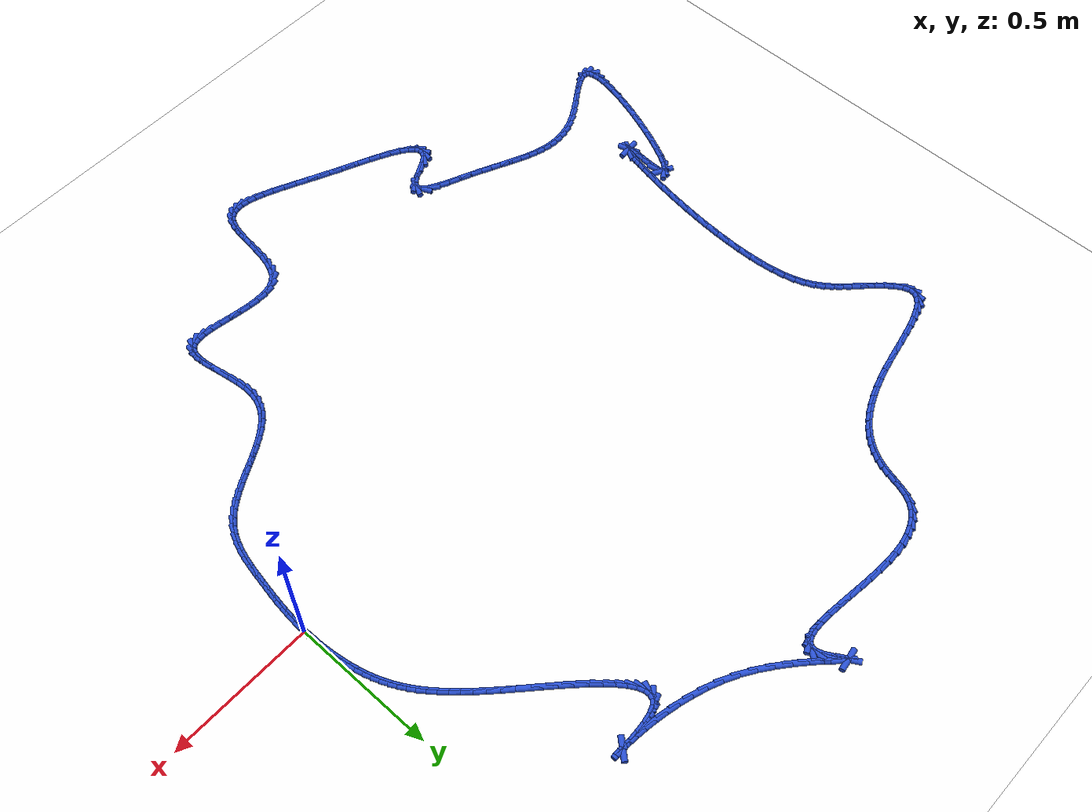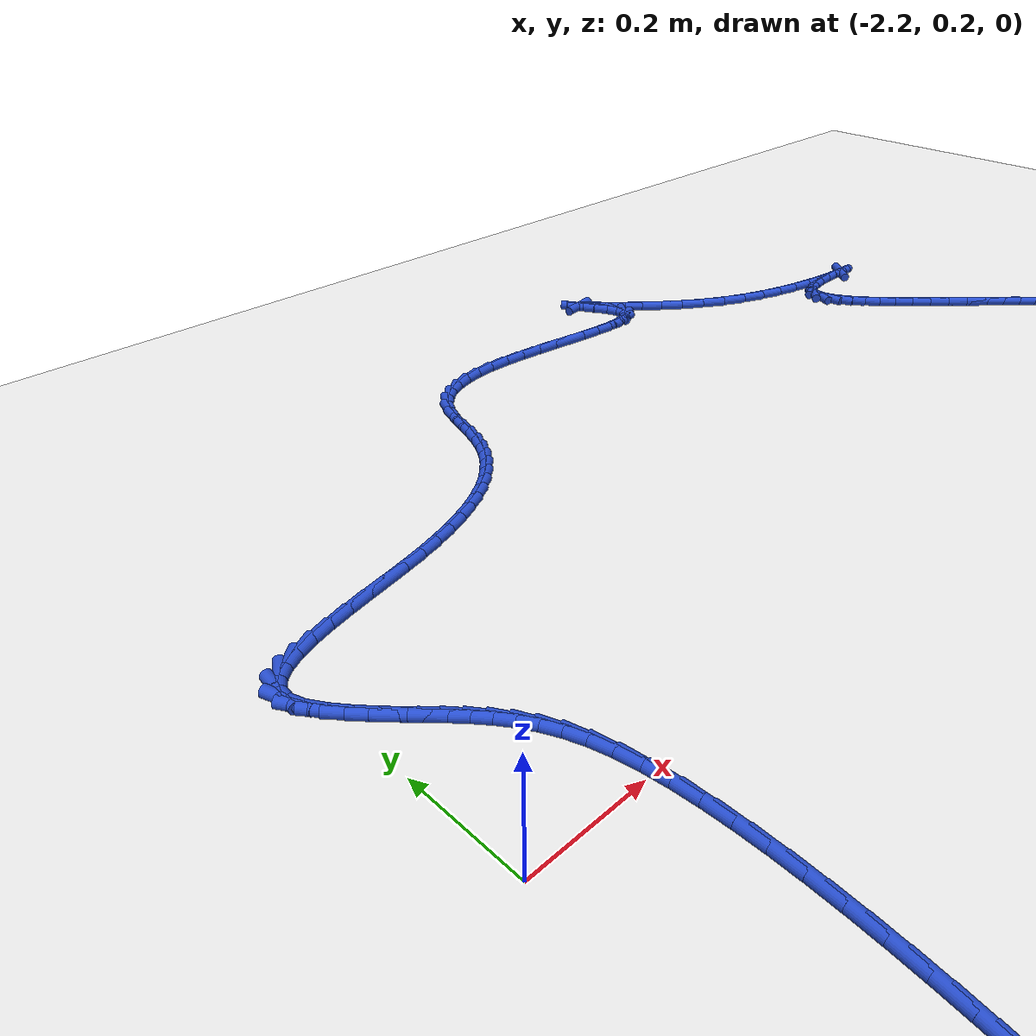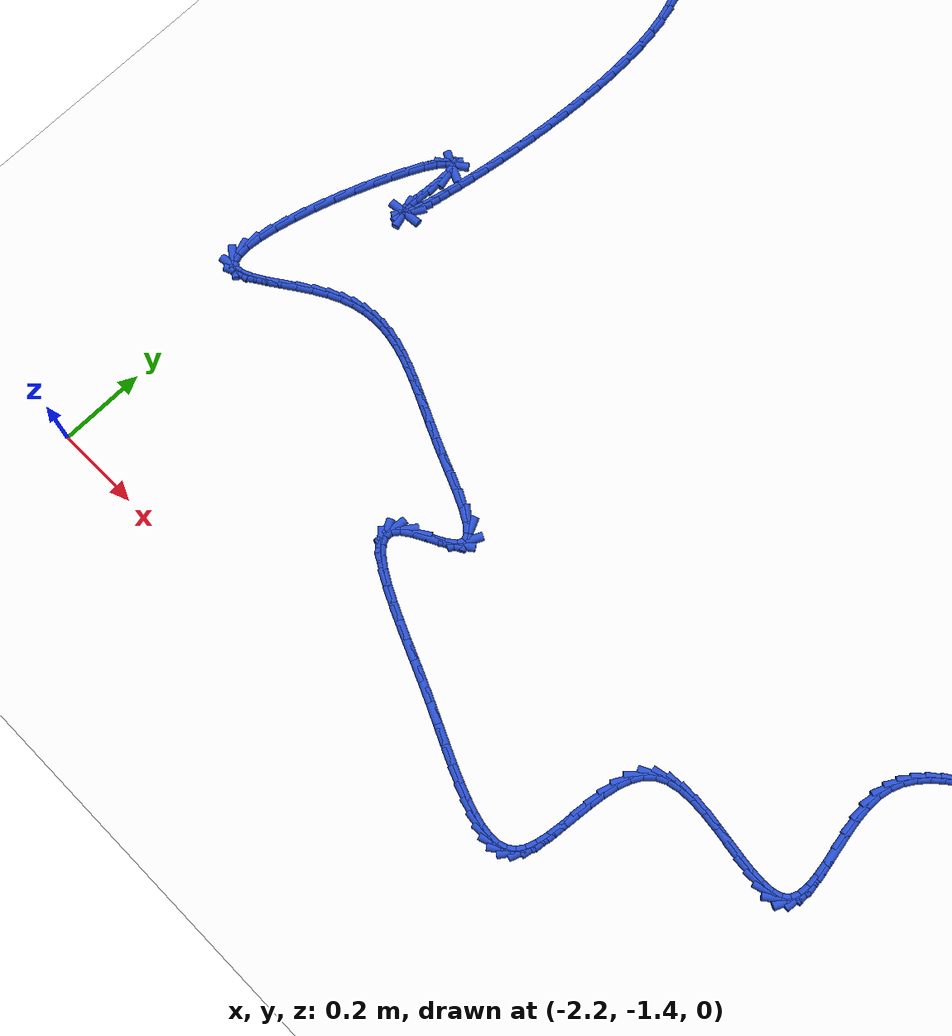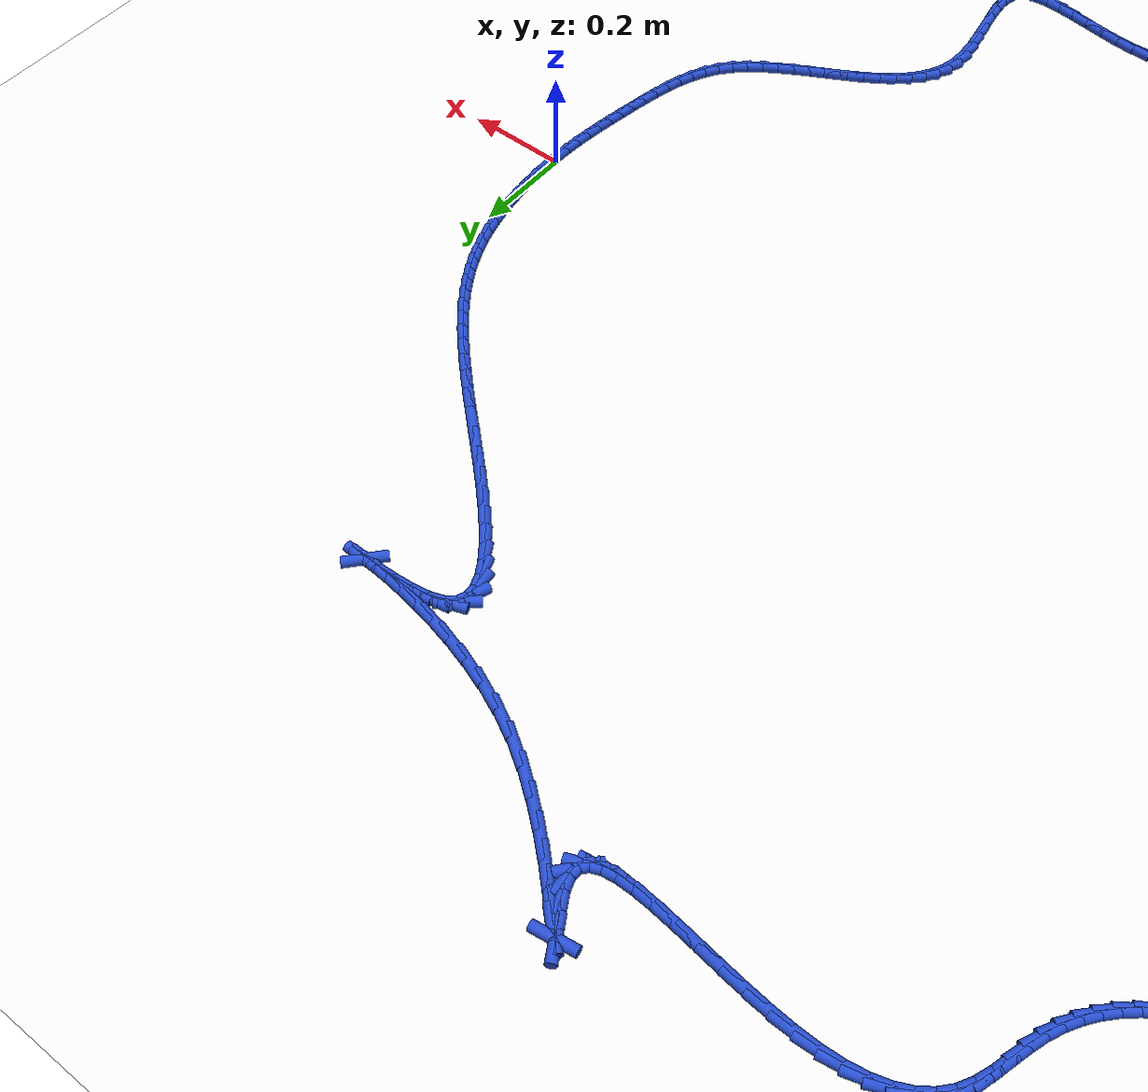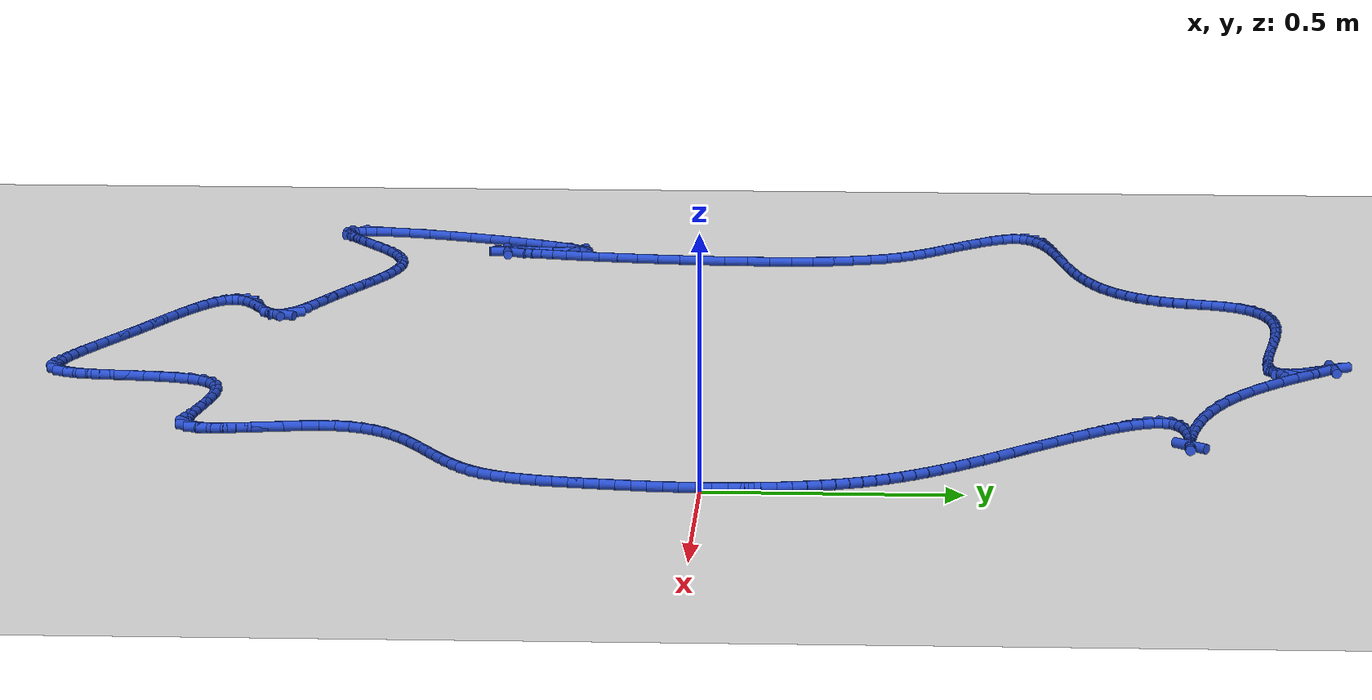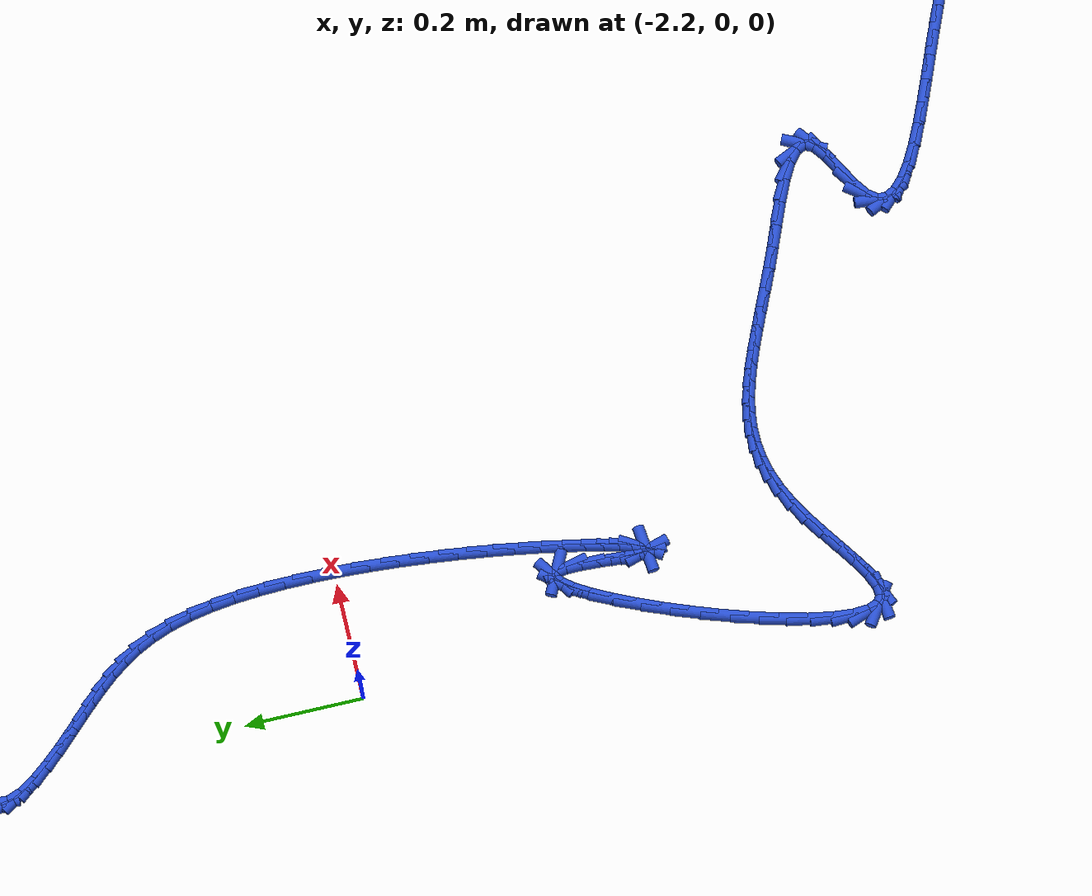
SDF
<sdf version="1.6">
 <world name="default">
  <light name="sun" type="directional">
   <pose>0 0 10 0 -0 0</pose>
   <diffuse>0.8 0.8 0.8 1</diffuse>
   <specular>0.2 0.2 0.2 1</specular>
   <attenuation>
    <range>1000</range>
    <constant>0.9</constant>
    <linear>0.01</linear>
    <quadratic>0.001</quadratic>
   </attenuation>
   <direction>-0.5 0.1 -0.9</direction>
  </light>
  <model name="ground_plane">
   <static>1</static>
   <link name="link">
    <collision name="collision">
     <geometry><plane><normal>0 0 1</normal><size>100 100</size></plane></geometry>
     <surface><friction><ode><mu>100</mu><mu2>50</mu2></ode></friction></surface>
    </collision>
    <visual name="visual">
     <cast_shadows>0</cast_shadows>
     <geometry><plane><normal>0 0 1</normal><size>100 100</size></plane></geometry>
     <material>
      <script><uri>file://media/materials/scripts/gazebo.material</uri><name>Gazebo/WhiteGlow</name></script>
     </material>
    </visual>
   </link>
  </model>
  <gravity>0 0 -9.8</gravity>
  <magnetic_field>6e-06 2.3e-05 -4.2e-05</magnetic_field>
  <atmosphere type="adiabatic"/>
  <physics name="default_physics" default="0" type="ode">
   <max_step_size>0.001</max_step_size>
   <real_time_factor>1</real_time_factor>
   <real_time_update_rate>1000</real_time_update_rate>
  </physics>
  <scene><ambient>0.4 0.4 0.4 1</ambient><background>0.7 0.7 0.7 1</background><shadows>1</shadows></scene>
  <spherical_coordinates>
   <surface_model>EARTH_WGS84</surface_model>
   <latitude_deg>0</latitude_deg>
   <longitude_deg>0</longitude_deg>
   <elevation>0</elevation>
   <heading_deg>0</heading_deg>
  </spherical_coordinates>
  <model name="line">
   <link name="link_0">
    <pose>1.8648277366750676e-17 -6.938893903907228e-18 0.01 0 1.57 -1.5699351642614259</pose>
    <collision name="collision">
     <geometry><cylinder><radius>0.01</radius><length>0.08</length></cylinder></geometry>
    </collision>
    <visual name="visual">
     <material>
      <script><name>Gazebo/Blue</name><uri>file://media/materials/scripts/gazebo.material</uri></script>
     </material>
     <geometry><cylinder><radius>0.01</radius><length>0.08</length></cylinder></geometry>
    </visual>
   </link>
   <link name="link_1">
    <pose>-2.6558653135063657e-05 0.030840457564657316 0.01 0 1.57 -1.5355909908459235</pose>
    <collision name="collision">
     <geometry><cylinder><radius>0.01</radius><length>0.08</length></cylinder></geometry>
    </collision>
    <visual name="visual">
     <material>
      <script><name>Gazebo/Blue</name><uri>file://media/materials/scripts/gazebo.material</uri></script>
     </material>
     <geometry><cylinder><radius>0.01</radius><length>0.08</length></cylinder></geometry>
    </visual>
   </link>
   <link name="link_2">
    <pose>-0.0011189718829572883 0.061857399885012196 0.01 0 1.57 -1.5012671882661344</pose>
    <collision name="collision">
     <geometry><cylinder><radius>0.01</radius><length>0.08</length></cylinder></geometry>
    </collision>
    <visual name="visual">
     <material>
      <script><name>Gazebo/Blue</name><uri>file://media/materials/scripts/gazebo.material</uri></script>
     </material>
     <geometry><cylinder><radius>0.01</radius><length>0.08</length></cylinder></geometry>
    </visual>
   </link>
   <link name="link_3">
    <pose>-0.0032751421259902946 0.09281844215993389 0.01 0 1.57 -1.4662702780033963</pose>
    <collision name="collision">
     <geometry><cylinder><radius>0.01</radius><length>0.08</length></cylinder></geometry>
    </collision>
    <visual name="visual">
     <material>
      <script><name>Gazebo/Blue</name><uri>file://media/materials/scripts/gazebo.material</uri></script>
     </material>
     <geometry><cylinder><radius>0.01</radius><length>0.08</length></cylinder></geometry>
    </visual>
   </link>
   <link name="link_4">
    <pose>-0.0064929718187577284 0.12349119958829174 0.01 0 1.57 -1.4298760749262927</pose>
    <collision name="collision">
     <geometry><cylinder><radius>0.01</radius><length>0.08</length></cylinder></geometry>
    </collision>
    <visual name="visual">
     <material>
      <script><name>Gazebo/Blue</name><uri>file://media/materials/scripts/gazebo.material</uri></script>
     </material>
     <geometry><cylinder><radius>0.01</radius><length>0.08</length></cylinder></geometry>
    </visual>
   </link>
   <link name="link_5">
    <pose>-0.01077036339778322 0.15364328736895494 0.01 0 1.57 -1.3912860349757676</pose>
    <collision name="collision">
     <geometry><cylinder><radius>0.01</radius><length>0.08</length></cylinder></geometry>
    </collision>
    <visual name="visual">
     <material>
      <script><name>Gazebo/Blue</name><uri>file://media/materials/scripts/gazebo.material</uri></script>
     </material>
     <geometry><cylinder><radius>0.01</radius><length>0.08</length></cylinder></geometry>
    </visual>
   </link>
   <link name="link_6">
    <pose>-0.016105219299590426 0.18304232070079293 0.01 0 1.57 -1.3495768886296635</pose>
    <collision name="collision">
     <geometry><cylinder><radius>0.01</radius><length>0.08</length></cylinder></geometry>
    </collision>
    <visual name="visual">
     <material>
      <script><name>Gazebo/Blue</name><uri>file://media/materials/scripts/gazebo.material</uri></script>
     </material>
     <geometry><cylinder><radius>0.01</radius><length>0.08</length></cylinder></geometry>
    </visual>
   </link>
   <link name="link_7">
    <pose>-0.022495441960702977 0.21145591478267486 0.01 0 1.57 -1.3037687663299813</pose>
    <collision name="collision">
     <geometry><cylinder><radius>0.01</radius><length>0.08</length></cylinder></geometry>
    </collision>
    <visual name="visual">
     <material>
      <script><name>Gazebo/Blue</name><uri>file://media/materials/scripts/gazebo.material</uri></script>
     </material>
     <geometry><cylinder><radius>0.01</radius><length>0.08</length></cylinder></geometry>
    </visual>
   </link>
   <link name="link_8">
    <pose>-0.029947641604828736 0.23869740522114524 0.01 0 1.57 -1.2540484309064965</pose>
    <collision name="collision">
     <geometry><cylinder><radius>0.01</radius><length>0.08</length></cylinder></geometry>
    </collision>
    <visual name="visual">
     <material>
      <script><name>Gazebo/Blue</name><uri>file://media/materials/scripts/gazebo.material</uri></script>
     </material>
     <geometry><cylinder><radius>0.01</radius><length>0.08</length></cylinder></geometry>
    </visual>
   </link>
   <link name="link_9">
    <pose>-0.03851952678452823 0.264848420402216 0.01 0 1.57 -1.201543858057164</pose>
    <collision name="collision">
     <geometry><cylinder><radius>0.01</radius><length>0.08</length></cylinder></geometry>
    </collision>
    <visual name="visual">
     <material>
      <script><name>Gazebo/Blue</name><uri>file://media/materials/scripts/gazebo.material</uri></script>
     </material>
     <geometry><cylinder><radius>0.01</radius><length>0.08</length></cylinder></geometry>
    </visual>
   </link>
   <link name="link_10">
    <pose>-0.04828738614631346 0.2900881438601974 0.01 0 1.57 -1.1475468493103482</pose>
    <collision name="collision">
     <geometry><cylinder><radius>0.01</radius><length>0.08</length></cylinder></geometry>
    </collision>
    <visual name="visual">
     <material>
      <script><name>Gazebo/Blue</name><uri>file://media/materials/scripts/gazebo.material</uri></script>
     </material>
     <geometry><cylinder><radius>0.01</radius><length>0.08</length></cylinder></geometry>
    </visual>
   </link>
   <link name="link_11">
    <pose>-0.059327534840524256 0.31459589828826795 0.01 0 1.57 -1.0935108847659418</pose>
    <collision name="collision">
     <geometry><cylinder><radius>0.01</radius><length>0.08</length></cylinder></geometry>
    </collision>
    <visual name="visual">
     <material>
      <script><name>Gazebo/Blue</name><uri>file://media/materials/scripts/gazebo.material</uri></script>
     </material>
     <geometry><cylinder><radius>0.01</radius><length>0.08</length></cylinder></geometry>
    </visual>
   </link>
   <link name="link_12">
    <pose>-0.07171628801750043 0.3385510063796065 0.01 0 1.57 -1.0409003785213045</pose>
    <collision name="collision">
     <geometry><cylinder><radius>0.01</radius><length>0.08</length></cylinder></geometry>
    </collision>
    <visual name="visual">
     <material>
      <script><name>Gazebo/Blue</name><uri>file://media/materials/scripts/gazebo.material</uri></script>
     </material>
     <geometry><cylinder><radius>0.01</radius><length>0.08</length></cylinder></geometry>
    </visual>
   </link>
   <link name="link_13">
    <pose>-0.08552996082758181 0.3621327908273916 0.01 0 1.57 -0.9910365975665014</pose>
    <collision name="collision">
     <geometry><cylinder><radius>0.01</radius><length>0.08</length></cylinder></geometry>
    </collision>
    <visual name="visual">
     <material>
      <script><name>Gazebo/Blue</name><uri>file://media/materials/scripts/gazebo.material</uri></script>
     </material>
     <geometry><cylinder><radius>0.01</radius><length>0.08</length></cylinder></geometry>
    </visual>
   </link>
   <link name="link_14">
    <pose>-0.10084486842110818 0.38552057432480186 0.01 0 1.57 -0.9449772846791378</pose>
    <collision name="collision">
     <geometry><cylinder><radius>0.01</radius><length>0.08</length></cylinder></geometry>
    </collision>
    <visual name="visual">
     <material>
      <script><name>Gazebo/Blue</name><uri>file://media/materials/scripts/gazebo.material</uri></script>
     </material>
     <geometry><cylinder><radius>0.01</radius><length>0.08</length></cylinder></geometry>
    </visual>
   </link>
   <link name="link_15">
    <pose>-0.11773732594841936 0.4088936795650161 0.01 0 1.57 -0.9034527363246793</pose>
    <collision name="collision">
     <geometry><cylinder><radius>0.01</radius><length>0.08</length></cylinder></geometry>
    </collision>
    <visual name="visual">
     <material>
      <script><name>Gazebo/Blue</name><uri>file://media/materials/scripts/gazebo.material</uri></script>
     </material>
     <geometry><cylinder><radius>0.01</radius><length>0.08</length></cylinder></geometry>
    </visual>
   </link>
   <link name="link_16">
    <pose>-0.13628364855985514 0.43243142924121275 0.01 0 1.57 -0.8668605858514146</pose>
    <collision name="collision">
     <geometry><cylinder><radius>0.01</radius><length>0.08</length></cylinder></geometry>
    </collision>
    <visual name="visual">
     <material>
      <script><name>Gazebo/Blue</name><uri>file://media/materials/scripts/gazebo.material</uri></script>
     </material>
     <geometry><cylinder><radius>0.01</radius><length>0.08</length></cylinder></geometry>
    </visual>
   </link>
   <link name="link_17">
    <pose>-0.1565601514057554 0.4563131460465707 0.01 0 1.57 -0.8353052364749499</pose>
    <collision name="collision">
     <geometry><cylinder><radius>0.01</radius><length>0.08</length></cylinder></geometry>
    </collision>
    <visual name="visual">
     <material>
      <script><name>Gazebo/Blue</name><uri>file://media/materials/scripts/gazebo.material</uri></script>
     </material>
     <geometry><cylinder><radius>0.01</radius><length>0.08</length></cylinder></geometry>
    </visual>
   </link>
   <link name="link_18">
    <pose>-0.17864314963645983 0.48071815267426843 0.01 0 1.57 -0.80866135174899</pose>
    <collision name="collision">
     <geometry><cylinder><radius>0.01</radius><length>0.08</length></cylinder></geometry>
    </collision>
    <visual name="visual">
     <material>
      <script><name>Gazebo/Blue</name><uri>file://media/materials/scripts/gazebo.material</uri></script>
     </material>
     <geometry><cylinder><radius>0.01</radius><length>0.08</length></cylinder></geometry>
    </visual>
   </link>
   <link name="link_19">
    <pose>-0.2026089584023083 0.5058257718174847 0.01 0 1.57 -0.7866429000537736</pose>
    <collision name="collision">
     <geometry><cylinder><radius>0.01</radius><length>0.08</length></cylinder></geometry>
    </collision>
    <visual name="visual">
     <material>
      <script><name>Gazebo/Blue</name><uri>file://media/materials/scripts/gazebo.material</uri></script>
     </material>
     <geometry><cylinder><radius>0.01</radius><length>0.08</length></cylinder></geometry>
    </visual>
   </link>
   <link name="link_20">
    <pose>-0.22853389285364079 0.5318153261693983 0.01 0 1.57 -0.7688655233514287</pose>
    <collision name="collision">
     <geometry><cylinder><radius>0.01</radius><length>0.08</length></cylinder></geometry>
    </collision>
    <visual name="visual">
     <material>
      <script><name>Gazebo/Blue</name><uri>file://media/materials/scripts/gazebo.material</uri></script>
     </material>
     <geometry><cylinder><radius>0.01</radius><length>0.08</length></cylinder></geometry>
    </visual>
   </link>
   <link name="link_21">
    <pose>-0.2564942681407969 0.5588661384231876 0.01 0 1.57 -0.7549696683386229</pose>
    <collision name="collision">
     <geometry><cylinder><radius>0.01</radius><length>0.08</length></cylinder></geometry>
    </collision>
    <visual name="visual">
     <material>
      <script><name>Gazebo/Blue</name><uri>file://media/materials/scripts/gazebo.material</uri></script>
     </material>
     <geometry><cylinder><radius>0.01</radius><length>0.08</length></cylinder></geometry>
    </visual>
   </link>
   <link name="link_22">
    <pose>-0.28655438236655634 0.5871503737709458 0.01 0 1.57 -0.7467585874671544</pose>
    <collision name="collision">
     <geometry><cylinder><radius>0.01</radius><length>0.08</length></cylinder></geometry>
    </collision>
    <visual name="visual">
     <material>
      <script><name>Gazebo/Blue</name><uri>file://media/materials/scripts/gazebo.material</uri></script>
     </material>
     <geometry><cylinder><radius>0.01</radius><length>0.08</length></cylinder></geometry>
    </visual>
   </link>
   <link name="link_23">
    <pose>-0.31836766330626554 0.6165954779926216 0.01 0 1.57 -0.7459757504787383</pose>
    <collision name="collision">
     <geometry><cylinder><radius>0.01</radius><length>0.08</length></cylinder></geometry>
    </collision>
    <visual name="visual">
     <material>
      <script><name>Gazebo/Blue</name><uri>file://media/materials/scripts/gazebo.material</uri></script>
     </material>
     <geometry><cylinder><radius>0.01</radius><length>0.08</length></cylinder></geometry>
    </visual>
   </link>
   <link name="link_24">
    <pose>-0.3510842617424648 0.6468291389114519 0.01 0 1.57 -0.7521501909869619</pose>
    <collision name="collision">
     <geometry><cylinder><radius>0.01</radius><length>0.08</length></cylinder></geometry>
    </collision>
    <visual name="visual">
     <material>
      <script><name>Gazebo/Blue</name><uri>file://media/materials/scripts/gazebo.material</uri></script>
     </material>
     <geometry><cylinder><radius>0.01</radius><length>0.08</length></cylinder></geometry>
    </visual>
   </link>
   <link name="link_25">
    <pose>-0.3838235913286182 0.6774607369391696 0.01 0 1.57 -0.7655263219053338</pose>
    <collision name="collision">
     <geometry><cylinder><radius>0.01</radius><length>0.08</length></cylinder></geometry>
    </collision>
    <visual name="visual">
     <material>
      <script><name>Gazebo/Blue</name><uri>file://media/materials/scripts/gazebo.material</uri></script>
     </material>
     <geometry><cylinder><radius>0.01</radius><length>0.08</length></cylinder></geometry>
    </visual>
   </link>
   <link name="link_26">
    <pose>-0.41570506571818994 0.7080996524875088 0.01 0 1.57 -0.7872621207988969</pose>
    <collision name="collision">
     <geometry><cylinder><radius>0.01</radius><length>0.08</length></cylinder></geometry>
    </collision>
    <visual name="visual">
     <material>
      <script><name>Gazebo/Blue</name><uri>file://media/materials/scripts/gazebo.material</uri></script>
     </material>
     <geometry><cylinder><radius>0.01</radius><length>0.08</length></cylinder></geometry>
    </visual>
   </link>
   <link name="link_27">
    <pose>-0.4458480985646444 0.7383552659682033 0.01 0 1.57 -0.8197266237173515</pose>
    <collision name="collision">
     <geometry><cylinder><radius>0.01</radius><length>0.08</length></cylinder></geometry>
    </collision>
    <visual name="visual">
     <material>
      <script><name>Gazebo/Blue</name><uri>file://media/materials/scripts/gazebo.material</uri></script>
     </material>
     <geometry><cylinder><radius>0.01</radius><length>0.08</length></cylinder></geometry>
    </visual>
   </link>
   <link name="link_28">
    <pose>-0.473372103521446 0.7678369577929868 0.01 0 1.57 -0.8672294111577838</pose>
    <collision name="collision">
     <geometry><cylinder><radius>0.01</radius><length>0.08</length></cylinder></geometry>
    </collision>
    <visual name="visual">
     <material>
      <script><name>Gazebo/Blue</name><uri>file://media/materials/scripts/gazebo.material</uri></script>
     </material>
     <geometry><cylinder><radius>0.01</radius><length>0.08</length></cylinder></geometry>
    </visual>
   </link>
   <link name="link_29">
    <pose>-0.4973964942420587 0.7961541083735928 0.01 0 1.57 -0.937592499780401</pose>
    <collision name="collision">
     <geometry><cylinder><radius>0.01</radius><length>0.08</length></cylinder></geometry>
    </collision>
    <visual name="visual">
     <material>
      <script><name>Gazebo/Blue</name><uri>file://media/materials/scripts/gazebo.material</uri></script>
     </material>
     <geometry><cylinder><radius>0.01</radius><length>0.08</length></cylinder></geometry>
    </visual>
   </link>
   <link name="link_30">
    <pose>-0.517040684379947 0.8229160981217555 0.01 0 1.57 -1.0455140600285147</pose>
    <collision name="collision">
     <geometry><cylinder><radius>0.01</radius><length>0.08</length></cylinder></geometry>
    </collision>
    <visual name="visual">
     <material>
      <script><name>Gazebo/Blue</name><uri>file://media/materials/scripts/gazebo.material</uri></script>
     </material>
     <geometry><cylinder><radius>0.01</radius><length>0.08</length></cylinder></geometry>
    </visual>
   </link>
   <link name="link_31">
    <pose>-0.5314240875885752 0.8477323074492085 0.01 0 1.57 -1.219373759275083</pose>
    <collision name="collision">
     <geometry><cylinder><radius>0.01</radius><length>0.08</length></cylinder></geometry>
    </collision>
    <visual name="visual">
     <material>
      <script><name>Gazebo/Blue</name><uri>file://media/materials/scripts/gazebo.material</uri></script>
     </material>
     <geometry><cylinder><radius>0.01</radius><length>0.08</length></cylinder></geometry>
    </visual>
   </link>
   <link name="link_32">
    <pose>-0.5396661175214075 0.8702121167676854 0.01 0 1.57 -1.5091077105702009</pose>
    <collision name="collision">
     <geometry><cylinder><radius>0.01</radius><length>0.08</length></cylinder></geometry>
    </collision>
    <visual name="visual">
     <material>
      <script><name>Gazebo/Blue</name><uri>file://media/materials/scripts/gazebo.material</uri></script>
     </material>
     <geometry><cylinder><radius>0.01</radius><length>0.08</length></cylinder></geometry>
    </visual>
   </link>
   <link name="link_33">
    <pose>-0.540886187831908 0.8899649064889201 0.01 0 1.57 1.1888182687031352</pose>
    <collision name="collision">
     <geometry><cylinder><radius>0.01</radius><length>0.08</length></cylinder></geometry>
    </collision>
    <visual name="visual">
     <material>
      <script><name>Gazebo/Blue</name><uri>file://media/materials/scripts/gazebo.material</uri></script>
     </material>
     <geometry><cylinder><radius>0.01</radius><length>0.08</length></cylinder></geometry>
    </visual>
   </link>
   <link name="link_34">
    <pose>-0.5342037121735415 0.9066000570246465 0.01 0 1.57 0.7037851027339573</pose>
    <collision name="collision">
     <geometry><cylinder><radius>0.01</radius><length>0.08</length></cylinder></geometry>
    </collision>
    <visual name="visual">
     <material>
      <script><name>Gazebo/Blue</name><uri>file://media/materials/scripts/gazebo.material</uri></script>
     </material>
     <geometry><cylinder><radius>0.01</radius><length>0.08</length></cylinder></geometry>
    </visual>
   </link>
   <link name="link_35">
    <pose>-0.5187381041997718 0.9197269487865981 0.01 0 1.57 0.3552605912063692</pose>
    <collision name="collision">
     <geometry><cylinder><radius>0.01</radius><length>0.08</length></cylinder></geometry>
    </collision>
    <visual name="visual">
     <material>
      <script><name>Gazebo/Blue</name><uri>file://media/materials/scripts/gazebo.material</uri></script>
     </material>
     <geometry><cylinder><radius>0.01</radius><length>0.08</length></cylinder></geometry>
    </visual>
   </link>
   <link name="link_36">
    <pose>-0.4937736977974682 0.9289887825739277 0.01 0 1.57 0.1749443810822862</pose>
    <collision name="collision">
     <geometry><cylinder><radius>0.01</radius><length>0.08</length></cylinder></geometry>
    </collision>
    <visual name="visual">
     <material>
      <script><name>Gazebo/Blue</name><uri>file://media/materials/scripts/gazebo.material</uri></script>
     </material>
     <geometry><cylinder><radius>0.01</radius><length>0.08</length></cylinder></geometry>
    </visual>
   </link>
   <link name="link_37">
    <pose>-0.46167985544530693 0.9346614096497076 0.01 0 1.57 0.0853910090603869</pose>
    <collision name="collision">
     <geometry><cylinder><radius>0.01</radius><length>0.08</length></cylinder></geometry>
    </collision>
    <visual name="visual">
     <material>
      <script><name>Gazebo/Blue</name><uri>file://media/materials/scripts/gazebo.material</uri></script>
     </material>
     <geometry><cylinder><radius>0.01</radius><length>0.08</length></cylinder></geometry>
    </visual>
   </link>
   <link name="link_38">
    <pose>-0.42756234777719987 0.9375818397354689 0.01 0 1.57 0.0331062924889678</pose>
    <collision name="collision">
     <geometry><cylinder><radius>0.01</radius><length>0.08</length></cylinder></geometry>
    </collision>
    <visual name="visual">
     <material>
      <script><name>Gazebo/Blue</name><uri>file://media/materials/scripts/gazebo.material</uri></script>
     </material>
     <geometry><cylinder><radius>0.01</radius><length>0.08</length></cylinder></geometry>
    </visual>
   </link>
   <link name="link_39">
    <pose>-0.396621827128156 0.9386065400554644 0.01 0 1.57 -0.0006803154684444225</pose>
    <collision name="collision">
     <geometry><cylinder><radius>0.01</radius><length>0.08</length></cylinder></geometry>
    </collision>
    <visual name="visual">
     <material>
      <script><name>Gazebo/Blue</name><uri>file://media/materials/scripts/gazebo.material</uri></script>
     </material>
     <geometry><cylinder><radius>0.01</radius><length>0.08</length></cylinder></geometry>
    </visual>
   </link>
   <link name="link_40">
    <pose>-0.3740484094236778 0.9385911830078552 0.01 0 1.57 -0.031224819922408456</pose>
    <collision name="collision">
     <geometry><cylinder><radius>0.01</radius><length>0.08</length></cylinder></geometry>
    </collision>
    <visual name="visual">
     <material>
      <script><name>Gazebo/Blue</name><uri>file://media/materials/scripts/gazebo.material</uri></script>
     </material>
     <geometry><cylinder><radius>0.01</radius><length>0.08</length></cylinder></geometry>
    </visual>
   </link>
   <link name="link_41">
    <pose>-0.363179800390428 0.9382517023107881 0.01 0 1.57 0.8553237310310862</pose>
    <collision name="collision">
     <geometry><cylinder><radius>0.01</radius><length>0.08</length></cylinder></geometry>
    </collision>
    <visual name="visual">
     <material>
      <script><name>Gazebo/Blue</name><uri>file://media/materials/scripts/gazebo.material</uri></script>
     </material>
     <geometry><cylinder><radius>0.01</radius><length>0.08</length></cylinder></geometry>
    </visual>
   </link>
   <link name="link_42">
    <pose>-0.363393927532335 0.9380053212875225 0.01 0 1.57 -0.022178151660232938</pose>
    <collision name="collision">
     <geometry><cylinder><radius>0.01</radius><length>0.08</length></cylinder></geometry>
    </collision>
    <visual name="visual">
     <material>
      <script><name>Gazebo/Blue</name><uri>file://media/materials/scripts/gazebo.material</uri></script>
     </material>
     <geometry><cylinder><radius>0.01</radius><length>0.08</length></cylinder></geometry>
    </visual>
   </link>
   <link name="link_43">
    <pose>-0.3735587878399767 0.9382307960703674 0.01 0 1.57 -0.05662450311762661</pose>
    <collision name="collision">
     <geometry><cylinder><radius>0.01</radius><length>0.08</length></cylinder></geometry>
    </collision>
    <visual name="visual">
     <material>
      <script><name>Gazebo/Blue</name><uri>file://media/materials/scripts/gazebo.material</uri></script>
     </material>
     <geometry><cylinder><radius>0.01</radius><length>0.08</length></cylinder></geometry>
    </visual>
   </link>
   <link name="link_44">
    <pose>-0.3925423783039315 0.9393068827916329 0.01 0 1.57 -0.0862283700839167</pose>
    <collision name="collision">
     <geometry><cylinder><radius>0.01</radius><length>0.08</length></cylinder></geometry>
    </collision>
    <visual name="visual">
     <material>
      <script><name>Gazebo/Blue</name><uri>file://media/materials/scripts/gazebo.material</uri></script>
     </material>
     <geometry><cylinder><radius>0.01</radius><length>0.08</length></cylinder></geometry>
    </visual>
   </link>
   <link name="link_45">
    <pose>-0.41921269591477733 0.9416123375836283 0.01 0 1.57 -0.11724977139653188</pose>
    <collision name="collision">
     <geometry><cylinder><radius>0.01</radius><length>0.08</length></cylinder></geometry>
    </collision>
    <visual name="visual">
     <material>
      <script><name>Gazebo/Blue</name><uri>file://media/materials/scripts/gazebo.material</uri></script>
     </material>
     <geometry><cylinder><radius>0.01</radius><length>0.08</length></cylinder></geometry>
    </visual>
   </link>
   <link name="link_46">
    <pose>-0.4524377376630921 0.9455259165786635 0.01 0 1.57 -0.15150283060369207</pose>
    <collision name="collision">
     <geometry><cylinder><radius>0.01</radius><length>0.08</length></cylinder></geometry>
    </collision>
    <visual name="visual">
     <material>
      <script><name>Gazebo/Blue</name><uri>file://media/materials/scripts/gazebo.material</uri></script>
     </material>
     <geometry><cylinder><radius>0.01</radius><length>0.08</length></cylinder></geometry>
    </visual>
   </link>
   <link name="link_47">
    <pose>-0.4910855005394544 0.9514263759090478 0.01 0 1.57 -0.1901835714295367</pose>
    <collision name="collision">
     <geometry><cylinder><radius>0.01</radius><length>0.08</length></cylinder></geometry>
    </collision>
    <visual name="visual">
     <material>
      <script><name>Gazebo/Blue</name><uri>file://media/materials/scripts/gazebo.material</uri></script>
     </material>
     <geometry><cylinder><radius>0.01</radius><length>0.08</length></cylinder></geometry>
    </visual>
   </link>
   <link name="link_48">
    <pose>-0.5340239815344421 0.9596924717070909 0.01 0 1.57 -0.23446088229895862</pose>
    <collision name="collision">
     <geometry><cylinder><radius>0.01</radius><length>0.08</length></cylinder></geometry>
    </collision>
    <visual name="visual">
     <material>
      <script><name>Gazebo/Blue</name><uri>file://media/materials/scripts/gazebo.material</uri></script>
     </material>
     <geometry><cylinder><radius>0.01</radius><length>0.08</length></cylinder></geometry>
    </visual>
   </link>
   <link name="link_49">
    <pose>-0.5801211776386332 0.9707029601051029 0.01 0 1.57 -0.2856602179161771</pose>
    <collision name="collision">
     <geometry><cylinder><radius>0.01</radius><length>0.08</length></cylinder></geometry>
    </collision>
    <visual name="visual">
     <material>
      <script><name>Gazebo/Blue</name><uri>file://media/materials/scripts/gazebo.material</uri></script>
     </material>
     <geometry><cylinder><radius>0.01</radius><length>0.08</length></cylinder></geometry>
    </visual>
   </link>
   <link name="link_50">
    <pose>-0.6282450858426063 0.9848365972353929 0.01 0 1.57 -0.34535401380363107</pose>
    <collision name="collision">
     <geometry><cylinder><radius>0.01</radius><length>0.08</length></cylinder></geometry>
    </collision>
    <visual name="visual">
     <material>
      <script><name>Gazebo/Blue</name><uri>file://media/materials/scripts/gazebo.material</uri></script>
     </material>
     <geometry><cylinder><radius>0.01</radius><length>0.08</length></cylinder></geometry>
    </visual>
   </link>
   <link name="link_51">
    <pose>-0.6772637031369386 1.0024721392302707 0.01 0 1.57 -0.41540682454194283</pose>
    <collision name="collision">
     <geometry><cylinder><radius>0.01</radius><length>0.08</length></cylinder></geometry>
    </collision>
    <visual name="visual">
     <material>
      <script><name>Gazebo/Blue</name><uri>file://media/materials/scripts/gazebo.material</uri></script>
     </material>
     <geometry><cylinder><radius>0.01</radius><length>0.08</length></cylinder></geometry>
    </visual>
   </link>
   <link name="link_52">
    <pose>-0.7260450265122089 1.023988342222046 0.01 0 1.57 -0.49740272231836274</pose>
    <collision name="collision">
     <geometry><cylinder><radius>0.01</radius><length>0.08</length></cylinder></geometry>
    </collision>
    <visual name="visual">
     <material>
      <script><name>Gazebo/Blue</name><uri>file://media/materials/scripts/gazebo.material</uri></script>
     </material>
     <geometry><cylinder><radius>0.01</radius><length>0.08</length></cylinder></geometry>
    </visual>
   </link>
   <link name="link_53">
    <pose>-0.77346371686025 1.0497336010303155 0.01 0 1.57 -0.5776562725409702</pose>
    <collision name="collision">
     <geometry><cylinder><radius>0.01</radius><length>0.08</length></cylinder></geometry>
    </collision>
    <visual name="visual">
     <material>
      <script><name>Gazebo/Blue</name><uri>file://media/materials/scripts/gazebo.material</uri></script>
     </material>
     <geometry><cylinder><radius>0.01</radius><length>0.08</length></cylinder></geometry>
    </visual>
   </link>
   <link name="link_54">
    <pose>-0.8185933242843307 1.079150153958692 0.01 0 1.57 -0.6417391335260849</pose>
    <collision name="collision">
     <geometry><cylinder><radius>0.01</radius><length>0.08</length></cylinder></geometry>
    </collision>
    <visual name="visual">
     <material>
      <script><name>Gazebo/Blue</name><uri>file://media/materials/scripts/gazebo.material</uri></script>
     </material>
     <geometry><cylinder><radius>0.01</radius><length>0.08</length></cylinder></geometry>
    </visual>
   </link>
   <link name="link_55">
    <pose>-0.8607355137920972 1.1106409280002376 0.01 0 1.57 -0.6924833207442543</pose>
    <collision name="collision">
     <geometry><cylinder><radius>0.01</radius><length>0.08</length></cylinder></geometry>
    </collision>
    <visual name="visual">
     <material>
      <script><name>Gazebo/Blue</name><uri>file://media/materials/scripts/gazebo.material</uri></script>
     </material>
     <geometry><cylinder><radius>0.01</radius><length>0.08</length></cylinder></geometry>
    </visual>
   </link>
   <link name="link_56">
    <pose>-0.8992044938945157 1.1425517008577826 0.01 0 1.57 -0.7324516487851053</pose>
    <collision name="collision">
     <geometry><cylinder><radius>0.01</radius><length>0.08</length></cylinder></geometry>
    </collision>
    <visual name="visual">
     <material>
      <script><name>Gazebo/Blue</name><uri>file://media/materials/scripts/gazebo.material</uri></script>
     </material>
     <geometry><cylinder><radius>0.01</radius><length>0.08</length></cylinder></geometry>
    </visual>
   </link>
   <link name="link_57">
    <pose>-0.9333144731025531 1.1732282502341584 0.01 0 1.57 -0.7629391555437544</pose>
    <collision name="collision">
     <geometry><cylinder><radius>0.01</radius><length>0.08</length></cylinder></geometry>
    </collision>
    <visual name="visual">
     <material>
      <script><name>Gazebo/Blue</name><uri>file://media/materials/scripts/gazebo.material</uri></script>
     </material>
     <geometry><cylinder><radius>0.01</radius><length>0.08</length></cylinder></geometry>
    </visual>
   </link>
   <link name="link_58">
    <pose>-0.9623796599271763 1.2010163538321958 0.01 0 1.57 -0.7834838815795583</pose>
    <collision name="collision">
     <geometry><cylinder><radius>0.01</radius><length>0.08</length></cylinder></geometry>
    </collision>
    <visual name="visual">
     <material>
      <script><name>Gazebo/Blue</name><uri>file://media/materials/scripts/gazebo.material</uri></script>
     </material>
     <geometry><cylinder><radius>0.01</radius><length>0.08</length></cylinder></geometry>
    </visual>
   </link>
   <link name="link_59">
    <pose>-0.9857142628793519 1.2242617893547254 0.01 0 1.57 -0.7892347633814933</pose>
    <collision name="collision">
     <geometry><cylinder><radius>0.01</radius><length>0.08</length></cylinder></geometry>
    </collision>
    <visual name="visual">
     <material>
      <script><name>Gazebo/Blue</name><uri>file://media/materials/scripts/gazebo.material</uri></script>
     </material>
     <geometry><cylinder><radius>0.01</radius><length>0.08</length></cylinder></geometry>
    </visual>
   </link>
   <link name="link_60">
    <pose>-1.002632490470047 1.2413103345045786 0.01 0 1.57 -0.7528733613338938</pose>
    <collision name="collision">
     <geometry><cylinder><radius>0.01</radius><length>0.08</length></cylinder></geometry>
    </collision>
    <visual name="visual">
     <material>
      <script><name>Gazebo/Blue</name><uri>file://media/materials/scripts/gazebo.material</uri></script>
     </material>
     <geometry><cylinder><radius>0.01</radius><length>0.08</length></cylinder></geometry>
    </visual>
   </link>
   <link name="link_61">
    <pose>-1.0124485512102286 1.250507766984587 0.01 0 1.57 0.15066748449436723</pose>
    <collision name="collision">
     <geometry><cylinder><radius>0.01</radius><length>0.08</length></cylinder></geometry>
    </collision>
    <visual name="visual">
     <material>
      <script><name>Gazebo/Blue</name><uri>file://media/materials/scripts/gazebo.material</uri></script>
     </material>
     <geometry><cylinder><radius>0.01</radius><length>0.08</length></cylinder></geometry>
    </visual>
   </link>
   <link name="link_62">
    <pose>-1.0144766536108631 1.250199864497581 0.01 0 1.57 -1.0587248045058342</pose>
    <collision name="collision">
     <geometry><cylinder><radius>0.01</radius><length>0.08</length></cylinder></geometry>
    </collision>
    <visual name="visual">
     <material>
      <script><name>Gazebo/Blue</name><uri>file://media/materials/scripts/gazebo.material</uri></script>
     </material>
     <geometry><cylinder><radius>0.01</radius><length>0.08</length></cylinder></geometry>
    </visual>
   </link>
   <link name="link_63">
    <pose>-1.0080310061829176 1.2387324047463908 0.01 0 1.57 -1.0088660010166173</pose>
    <collision name="collision">
     <geometry><cylinder><radius>0.01</radius><length>0.08</length></cylinder></geometry>
    </collision>
    <visual name="visual">
     <material>
      <script><name>Gazebo/Blue</name><uri>file://media/materials/scripts/gazebo.material</uri></script>
     </material>
     <geometry><cylinder><radius>0.01</radius><length>0.08</length></cylinder></geometry>
    </visual>
   </link>
   <link name="link_64">
    <pose>-0.9934471232958112 1.2155702174096747 0.01 0 1.57 -1.060344816596319</pose>
    <collision name="collision">
     <geometry><cylinder><radius>0.01</radius><length>0.08</length></cylinder></geometry>
    </collision>
    <visual name="visual">
     <material>
      <script><name>Gazebo/Blue</name><uri>file://media/materials/scripts/gazebo.material</uri></script>
     </material>
     <geometry><cylinder><radius>0.01</radius><length>0.08</length></cylinder></geometry>
    </visual>
   </link>
   <link name="link_65">
    <pose>-0.9777074352610932 1.187461204476533 0.01 0 1.57 -1.2472370324191147</pose>
    <collision name="collision">
     <geometry><cylinder><radius>0.01</radius><length>0.08</length></cylinder></geometry>
    </collision>
    <visual name="visual">
     <material>
      <script><name>Gazebo/Blue</name><uri>file://media/materials/scripts/gazebo.material</uri></script>
     </material>
     <geometry><cylinder><radius>0.01</radius><length>0.08</length></cylinder></geometry>
    </visual>
   </link>
   <link name="link_66">
    <pose>-0.9695745295339376 1.1632087966651505 0.01 0 1.57 1.4844358170257046</pose>
    <collision name="collision">
     <geometry><cylinder><radius>0.01</radius><length>0.08</length></cylinder></geometry>
    </collision>
    <visual name="visual">
     <material>
      <script><name>Gazebo/Blue</name><uri>file://media/materials/scripts/gazebo.material</uri></script>
     </material>
     <geometry><cylinder><radius>0.01</radius><length>0.08</length></cylinder></geometry>
    </visual>
   </link>
   <link name="link_67">
    <pose>-0.9711418060684116 1.1451058665340856 0.01 0 1.57 0.8875218449737373</pose>
    <collision name="collision">
     <geometry><cylinder><radius>0.01</radius><length>0.08</length></cylinder></geometry>
    </collision>
    <visual name="visual">
     <material>
      <script><name>Gazebo/Blue</name><uri>file://media/materials/scripts/gazebo.material</uri></script>
     </material>
     <geometry><cylinder><radius>0.01</radius><length>0.08</length></cylinder></geometry>
    </visual>
   </link>
   <link name="link_68">
    <pose>-0.9814403913416481 1.1324554646187974 0.01 0 1.57 0.41314331284650657</pose>
    <collision name="collision">
     <geometry><cylinder><radius>0.01</radius><length>0.08</length></cylinder></geometry>
    </collision>
    <visual name="visual">
     <material>
      <script><name>Gazebo/Blue</name><uri>file://media/materials/scripts/gazebo.material</uri></script>
     </material>
     <geometry><cylinder><radius>0.01</radius><length>0.08</length></cylinder></geometry>
    </visual>
   </link>
   <link name="link_69">
    <pose>-0.9994854027345242 1.1245450111235813 0.01 0 1.57 0.1552745756650453</pose>
    <collision name="collision">
     <geometry><cylinder><radius>0.01</radius><length>0.08</length></cylinder></geometry>
    </collision>
    <visual name="visual">
     <material>
      <script><name>Gazebo/Blue</name><uri>file://media/materials/scripts/gazebo.material</uri></script>
     </material>
     <geometry><cylinder><radius>0.01</radius><length>0.08</length></cylinder></geometry>
    </visual>
   </link>
   <link name="link_70">
    <pose>-1.0242919576279166 1.1206619262527326 0.01 0 1.57 0.018579820091273836</pose>
    <collision name="collision">
     <geometry><cylinder><radius>0.01</radius><length>0.08</length></cylinder></geometry>
    </collision>
    <visual name="visual">
     <material>
      <script><name>Gazebo/Blue</name><uri>file://media/materials/scripts/gazebo.material</uri></script>
     </material>
     <geometry><cylinder><radius>0.01</radius><length>0.08</length></cylinder></geometry>
    </visual>
   </link>
   <link name="link_71">
    <pose>-1.0548751734027026 1.120093630210548 0.01 0 1.57 -0.057432552799085906</pose>
    <collision name="collision">
     <geometry><cylinder><radius>0.01</radius><length>0.08</length></cylinder></geometry>
    </collision>
    <visual name="visual">
     <material>
      <script><name>Gazebo/Blue</name><uri>file://media/materials/scripts/gazebo.material</uri></script>
     </material>
     <geometry><cylinder><radius>0.01</radius><length>0.08</length></cylinder></geometry>
    </visual>
   </link>
   <link name="link_72">
    <pose>-1.0902501674397589 1.1221275432013216 0.01 0 1.57 -0.09980392380520862</pose>
    <collision name="collision">
     <geometry><cylinder><radius>0.01</radius><length>0.08</length></cylinder></geometry>
    </collision>
    <visual name="visual">
     <material>
      <script><name>Gazebo/Blue</name><uri>file://media/materials/scripts/gazebo.material</uri></script>
     </material>
     <geometry><cylinder><radius>0.01</radius><length>0.08</length></cylinder></geometry>
    </visual>
   </link>
   <link name="link_73">
    <pose>-1.1294320571199623 1.1260510854293497 0.01 0 1.57 -0.1208397421972083</pose>
    <collision name="collision">
     <geometry><cylinder><radius>0.01</radius><length>0.08</length></cylinder></geometry>
    </collision>
    <visual name="visual">
     <material>
      <script><name>Gazebo/Blue</name><uri>file://media/materials/scripts/gazebo.material</uri></script>
     </material>
     <geometry><cylinder><radius>0.01</radius><length>0.08</length></cylinder></geometry>
    </visual>
   </link>
   <link name="link_74">
    <pose>-1.1714359598241897 1.1311516770989276 0.01 0 1.57 -0.12626200919075067</pose>
    <collision name="collision">
     <geometry><cylinder><radius>0.01</radius><length>0.08</length></cylinder></geometry>
    </collision>
    <visual name="visual">
     <material>
      <script><name>Gazebo/Blue</name><uri>file://media/materials/scripts/gazebo.material</uri></script>
     </material>
     <geometry><cylinder><radius>0.01</radius><length>0.08</length></cylinder></geometry>
    </visual>
   </link>
   <link name="link_75">
    <pose>-1.215276992933318 1.136716738414351 0.01 0 1.57 -0.11840882488628839</pose>
    <collision name="collision">
     <geometry><cylinder><radius>0.01</radius><length>0.08</length></cylinder></geometry>
    </collision>
    <visual name="visual">
     <material>
      <script><name>Gazebo/Blue</name><uri>file://media/materials/scripts/gazebo.material</uri></script>
     </material>
     <geometry><cylinder><radius>0.01</radius><length>0.08</length></cylinder></geometry>
    </visual>
   </link>
   <link name="link_76">
    <pose>-1.2599702738282228 1.1420336895799152 0.01 0 1.57 -0.09745061935984639</pose>
    <collision name="collision">
     <geometry><cylinder><radius>0.01</radius><length>0.08</length></cylinder></geometry>
    </collision>
    <visual name="visual">
     <material>
      <script><name>Gazebo/Blue</name><uri>file://media/materials/scripts/gazebo.material</uri></script>
     </material>
     <geometry><cylinder><radius>0.01</radius><length>0.08</length></cylinder></geometry>
    </visual>
   </link>
   <link name="link_77">
    <pose>-1.3045309198897832 1.1463899507999158 0.01 0 1.57 -0.06168036809671838</pose>
    <collision name="collision">
     <geometry><cylinder><radius>0.01</radius><length>0.08</length></cylinder></geometry>
    </collision>
    <visual name="visual">
     <material>
      <script><name>Gazebo/Blue</name><uri>file://media/materials/scripts/gazebo.material</uri></script>
     </material>
     <geometry><cylinder><radius>0.01</radius><length>0.08</length></cylinder></geometry>
    </visual>
   </link>
   <link name="link_78">
    <pose>-1.347974048498875 1.1490729422786488 0.01 0 1.57 -0.007187508189697457</pose>
    <collision name="collision">
     <geometry><cylinder><radius>0.01</radius><length>0.08</length></cylinder></geometry>
    </collision>
    <visual name="visual">
     <material>
      <script><name>Gazebo/Blue</name><uri>file://media/materials/scripts/gazebo.material</uri></script>
     </material>
     <geometry><cylinder><radius>0.01</radius><length>0.08</length></cylinder></geometry>
    </visual>
   </link>
   <link name="link_79">
    <pose>-1.389314777036375 1.149370084220409 0.01 0 1.57 0.07226812401409972</pose>
    <collision name="collision">
     <geometry><cylinder><radius>0.01</radius><length>0.08</length></cylinder></geometry>
    </collision>
    <visual name="visual">
     <material>
      <script><name>Gazebo/Blue</name><uri>file://media/materials/scripts/gazebo.material</uri></script>
     </material>
     <geometry><cylinder><radius>0.01</radius><length>0.08</length></cylinder></geometry>
    </visual>
   </link>
   <link name="link_80">
    <pose>-1.4276071407014916 1.1465979392427885 0.01 0 1.57 0.17601145373974536</pose>
    <collision name="collision">
     <geometry><cylinder><radius>0.01</radius><length>0.08</length></cylinder></geometry>
    </collision>
    <visual name="visual">
     <material>
      <script><name>Gazebo/Blue</name><uri>file://media/materials/scripts/gazebo.material</uri></script>
     </material>
     <geometry><cylinder><radius>0.01</radius><length>0.08</length></cylinder></geometry>
    </visual>
   </link>
   <link name="link_81">
    <pose>-1.4623636971600715 1.1404164204337106 0.01 0 1.57 0.3031713009041322</pose>
    <collision name="collision">
     <geometry><cylinder><radius>0.01</radius><length>0.08</length></cylinder></geometry>
    </collision>
    <visual name="visual">
     <material>
      <script><name>Gazebo/Blue</name><uri>file://media/materials/scripts/gazebo.material</uri></script>
     </material>
     <geometry><cylinder><radius>0.01</radius><length>0.08</length></cylinder></geometry>
    </visual>
   </link>
   <link name="link_82">
    <pose>-1.4933957489073275 1.1307091467736887 0.01 0 1.57 0.45724473415530625</pose>
    <collision name="collision">
     <geometry><cylinder><radius>0.01</radius><length>0.08</length></cylinder></geometry>
    </collision>
    <visual name="visual">
     <material>
      <script><name>Gazebo/Blue</name><uri>file://media/materials/scripts/gazebo.material</uri></script>
     </material>
     <geometry><cylinder><radius>0.01</radius><length>0.08</length></cylinder></geometry>
    </visual>
   </link>
   <link name="link_83">
    <pose>-1.5205197105454213 1.117363565287558 0.01 0 1.57 0.6385430067446697</pose>
    <collision name="collision">
     <geometry><cylinder><radius>0.01</radius><length>0.08</length></cylinder></geometry>
    </collision>
    <visual name="visual">
     <material>
      <script><name>Gazebo/Blue</name><uri>file://media/materials/scripts/gazebo.material</uri></script>
     </material>
     <geometry><cylinder><radius>0.01</radius><length>0.08</length></cylinder></geometry>
    </visual>
   </link>
   <link name="link_84">
    <pose>-1.5435519966765114 1.1002671230001528 0.01 0 1.57 0.8408047350247374</pose>
    <collision name="collision">
     <geometry><cylinder><radius>0.01</radius><length>0.08</length></cylinder></geometry>
    </collision>
    <visual name="visual">
     <material>
      <script><name>Gazebo/Blue</name><uri>file://media/materials/scripts/gazebo.material</uri></script>
     </material>
     <geometry><cylinder><radius>0.01</radius><length>0.08</length></cylinder></geometry>
    </visual>
   </link>
   <link name="link_85">
    <pose>-1.562309021902759 1.0793072669363095 0.01 0 1.57 1.046908763084747</pose>
    <collision name="collision">
     <geometry><cylinder><radius>0.01</radius><length>0.08</length></cylinder></geometry>
    </collision>
    <visual name="visual">
     <material>
      <script><name>Gazebo/Blue</name><uri>file://media/materials/scripts/gazebo.material</uri></script>
     </material>
     <geometry><cylinder><radius>0.01</radius><length>0.08</length></cylinder></geometry>
    </visual>
   </link>
   <link name="link_86">
    <pose>-1.5766790458229822 1.0544342466703833 0.01 0 1.57 1.2008478951903148</pose>
    <collision name="collision">
     <geometry><cylinder><radius>0.01</radius><length>0.08</length></cylinder></geometry>
    </collision>
    <visual name="visual">
     <material>
      <script><name>Gazebo/Blue</name><uri>file://media/materials/scripts/gazebo.material</uri></script>
     </material>
     <geometry><cylinder><radius>0.01</radius><length>0.08</length></cylinder></geometry>
    </visual>
   </link>
   <link name="link_87">
    <pose>-1.5875297225158906 1.0264544391785904 0.01 0 1.57 1.2790800485252356</pose>
    <collision name="collision">
     <geometry><cylinder><radius>0.01</radius><length>0.08</length></cylinder></geometry>
    </collision>
    <visual name="visual">
     <material>
      <script><name>Gazebo/Blue</name><uri>file://media/materials/scripts/gazebo.material</uri></script>
     </material>
     <geometry><cylinder><radius>0.01</radius><length>0.08</length></cylinder></geometry>
    </visual>
   </link>
   <link name="link_88">
    <pose>-1.596436551232766 0.9967929768630276 0.01 0 1.57 1.292182968399963</pose>
    <collision name="collision">
     <geometry><cylinder><radius>0.01</radius><length>0.08</length></cylinder></geometry>
    </collision>
    <visual name="visual">
     <material>
      <script><name>Gazebo/Blue</name><uri>file://media/materials/scripts/gazebo.material</uri></script>
     </material>
     <geometry><cylinder><radius>0.01</radius><length>0.08</length></cylinder></geometry>
    </visual>
   </link>
   <link name="link_89">
    <pose>-1.6049907649490731 0.9668887455955971 0.01 0 1.57 1.2422692446020063</pose>
    <collision name="collision">
     <geometry><cylinder><radius>0.01</radius><length>0.08</length></cylinder></geometry>
    </collision>
    <visual name="visual">
     <material>
      <script><name>Gazebo/Blue</name><uri>file://media/materials/scripts/gazebo.material</uri></script>
     </material>
     <geometry><cylinder><radius>0.01</radius><length>0.08</length></cylinder></geometry>
    </visual>
   </link>
   <link name="link_90">
    <pose>-1.6147784689903848 0.9381756944385862 0.01 0 1.57 1.1444239049834506</pose>
    <collision name="collision">
     <geometry><cylinder><radius>0.01</radius><length>0.08</length></cylinder></geometry>
    </collision>
    <visual name="visual">
     <material>
      <script><name>Gazebo/Blue</name><uri>file://media/materials/scripts/gazebo.material</uri></script>
     </material>
     <geometry><cylinder><radius>0.01</radius><length>0.08</length></cylinder></geometry>
    </visual>
   </link>
   <link name="link_91">
    <pose>-1.6268589721160207 0.9115805821413625 0.01 0 1.57 1.0375486268130099</pose>
    <collision name="collision">
     <geometry><cylinder><radius>0.01</radius><length>0.08</length></cylinder></geometry>
    </collision>
    <visual name="visual">
     <material>
      <script><name>Gazebo/Blue</name><uri>file://media/materials/scripts/gazebo.material</uri></script>
     </material>
     <geometry><cylinder><radius>0.01</radius><length>0.08</length></cylinder></geometry>
    </visual>
   </link>
   <link name="link_92">
    <pose>-1.6413153246723198 0.8870902433123828 0.01 0 1.57 0.9291794185078801</pose>
    <collision name="collision">
     <geometry><cylinder><radius>0.01</radius><length>0.08</length></cylinder></geometry>
    </collision>
    <visual name="visual">
     <material>
      <script><name>Gazebo/Blue</name><uri>file://media/materials/scripts/gazebo.material</uri></script>
     </material>
     <geometry><cylinder><radius>0.01</radius><length>0.08</length></cylinder></geometry>
    </visual>
   </link>
   <link name="link_93">
    <pose>-1.6581246855259126 0.8645895621371701 0.01 0 1.57 0.8227650540368983</pose>
    <collision name="collision">
     <geometry><cylinder><radius>0.01</radius><length>0.08</length></cylinder></geometry>
    </collision>
    <visual name="visual">
     <material>
      <script><name>Gazebo/Blue</name><uri>file://media/materials/scripts/gazebo.material</uri></script>
     </material>
     <geometry><cylinder><radius>0.01</radius><length>0.08</length></cylinder></geometry>
    </visual>
   </link>
   <link name="link_94">
    <pose>-1.67726421354343 0.8439634228012481 0.01 0 1.57 0.7214835413718582</pose>
    <collision name="collision">
     <geometry><cylinder><radius>0.01</radius><length>0.08</length></cylinder></geometry>
    </collision>
    <visual name="visual">
     <material>
      <script><name>Gazebo/Blue</name><uri>file://media/materials/scripts/gazebo.material</uri></script>
     </material>
     <geometry><cylinder><radius>0.01</radius><length>0.08</length></cylinder></geometry>
    </visual>
   </link>
   <link name="link_95">
    <pose>-1.698711067591501 0.82509670949014 0.01 0 1.57 0.6277826128086919</pose>
    <collision name="collision">
     <geometry><cylinder><radius>0.01</radius><length>0.08</length></cylinder></geometry>
    </collision>
    <visual name="visual">
     <material>
      <script><name>Gazebo/Blue</name><uri>file://media/materials/scripts/gazebo.material</uri></script>
     </material>
     <geometry><cylinder><radius>0.01</radius><length>0.08</length></cylinder></geometry>
    </visual>
   </link>
   <link name="link_96">
    <pose>-1.7224424065367563 0.8078743063893696 0.01 0 1.57 0.5431707524089897</pose>
    <collision name="collision">
     <geometry><cylinder><radius>0.01</radius><length>0.08</length></cylinder></geometry>
    </collision>
    <visual name="visual">
     <material>
      <script><name>Gazebo/Blue</name><uri>file://media/materials/scripts/gazebo.material</uri></script>
     </material>
     <geometry><cylinder><radius>0.01</radius><length>0.08</length></cylinder></geometry>
    </visual>
   </link>
   <link name="link_97">
    <pose>-1.7484353892458258 0.7921810976844603 0.01 0 1.57 0.46826253868430623</pose>
    <collision name="collision">
     <geometry><cylinder><radius>0.01</radius><length>0.08</length></cylinder></geometry>
    </collision>
    <visual name="visual">
     <material>
      <script><name>Gazebo/Blue</name><uri>file://media/materials/scripts/gazebo.material</uri></script>
     </material>
     <geometry><cylinder><radius>0.01</radius><length>0.08</length></cylinder></geometry>
    </visual>
   </link>
   <link name="link_98">
    <pose>-1.77666717458534 0.7779019675609352 0.01 0 1.57 0.40297938345953266</pose>
    <collision name="collision">
     <geometry><cylinder><radius>0.01</radius><length>0.08</length></cylinder></geometry>
    </collision>
    <visual name="visual">
     <material>
      <script><name>Gazebo/Blue</name><uri>file://media/materials/scripts/gazebo.material</uri></script>
     </material>
     <geometry><cylinder><radius>0.01</radius><length>0.08</length></cylinder></geometry>
    </visual>
   </link>
   <link name="link_99">
    <pose>-1.807114921421929 0.7649218002043182 0.01 0 1.57 0.34679199227225677</pose>
    <collision name="collision">
     <geometry><cylinder><radius>0.01</radius><length>0.08</length></cylinder></geometry>
    </collision>
    <visual name="visual">
     <material>
      <script><name>Gazebo/Blue</name><uri>file://media/materials/scripts/gazebo.material</uri></script>
     </material>
     <geometry><cylinder><radius>0.01</radius><length>0.08</length></cylinder></geometry>
    </visual>
   </link>
   <link name="link_100">
    <pose>-1.8397557886222233 0.7531254798001326 0.01 0 1.57 0.29893100838939557</pose>
    <collision name="collision">
     <geometry><cylinder><radius>0.01</radius><length>0.08</length></cylinder></geometry>
    </collision>
    <visual name="visual">
     <material>
      <script><name>Gazebo/Blue</name><uri>file://media/materials/scripts/gazebo.material</uri></script>
     </material>
     <geometry><cylinder><radius>0.01</radius><length>0.08</length></cylinder></geometry>
    </visual>
   </link>
   <link name="link_101">
    <pose>-1.8745669350528518 0.7423978905339018 0.01 0 1.57 0.25853873628662183</pose>
    <collision name="collision">
     <geometry><cylinder><radius>0.01</radius><length>0.08</length></cylinder></geometry>
    </collision>
    <visual name="visual">
     <material>
      <script><name>Gazebo/Blue</name><uri>file://media/materials/scripts/gazebo.material</uri></script>
     </material>
     <geometry><cylinder><radius>0.01</radius><length>0.08</length></cylinder></geometry>
    </visual>
   </link>
   <link name="link_102">
    <pose>-1.911525519580446 0.7326239165911491 0.01 0 1.57 0.22483075040479214</pose>
    <collision name="collision">
     <geometry><cylinder><radius>0.01</radius><length>0.08</length></cylinder></geometry>
    </collision>
    <visual name="visual">
     <material>
      <script><name>Gazebo/Blue</name><uri>file://media/materials/scripts/gazebo.material</uri></script>
     </material>
     <geometry><cylinder><radius>0.01</radius><length>0.08</length></cylinder></geometry>
    </visual>
   </link>
   <link name="link_103">
    <pose>-1.950602851935562 0.7236870376928374 0.01 0 1.57 0.20137429749580496</pose>
    <collision name="collision">
     <geometry><cylinder><radius>0.01</radius><length>0.08</length></cylinder></geometry>
    </collision>
    <visual name="visual">
     <material>
      <script><name>Gazebo/Blue</name><uri>file://media/materials/scripts/gazebo.material</uri></script>
     </material>
     <geometry><cylinder><radius>0.01</radius><length>0.08</length></cylinder></geometry>
    </visual>
   </link>
   <link name="link_104">
    <pose>-1.9913478358668344 0.7153693076015942 0.01 0 1.57 0.1934794579846722</pose>
    <collision name="collision">
     <geometry><cylinder><radius>0.01</radius><length>0.08</length></cylinder></geometry>
    </collision>
    <visual name="visual">
     <material>
      <script><name>Gazebo/Blue</name><uri>file://media/materials/scripts/gazebo.material</uri></script>
     </material>
     <geometry><cylinder><radius>0.01</radius><length>0.08</length></cylinder></geometry>
    </visual>
   </link>
   <link name="link_105">
    <pose>-2.0326098732124094 0.7072848192682542 0.01 0 1.57 0.2007211011636959</pose>
    <collision name="collision">
     <geometry><cylinder><radius>0.01</radius><length>0.08</length></cylinder></geometry>
    </collision>
    <visual name="visual">
     <material>
      <script><name>Gazebo/Blue</name><uri>file://media/materials/scripts/gazebo.material</uri></script>
     </material>
     <geometry><cylinder><radius>0.01</radius><length>0.08</length></cylinder></geometry>
    </visual>
   </link>
   <link name="link_106">
    <pose>-2.073172638289756 0.6990318834884297 0.01 0 1.57 0.22445133653969696</pose>
    <collision name="collision">
     <geometry><cylinder><radius>0.01</radius><length>0.08</length></cylinder></geometry>
    </collision>
    <visual name="visual">
     <material>
      <script><name>Gazebo/Blue</name><uri>file://media/materials/scripts/gazebo.material</uri></script>
     </material>
     <geometry><cylinder><radius>0.01</radius><length>0.08</length></cylinder></geometry>
    </visual>
   </link>
   <link name="link_107">
    <pose>-2.111819805416342 0.6902088110577328 0.01 0 1.57 0.2691044254078841</pose>
    <collision name="collision">
     <geometry><cylinder><radius>0.01</radius><length>0.08</length></cylinder></geometry>
    </collision>
    <visual name="visual">
     <material>
      <script><name>Gazebo/Blue</name><uri>file://media/materials/scripts/gazebo.material</uri></script>
     </material>
     <geometry><cylinder><radius>0.01</radius><length>0.08</length></cylinder></geometry>
    </visual>
   </link>
   <link name="link_108">
    <pose>-2.1473350489096363 0.6804139127717761 0.01 0 1.57 0.34408618547369274</pose>
    <collision name="collision">
     <geometry><cylinder><radius>0.01</radius><length>0.08</length></cylinder></geometry>
    </collision>
    <visual name="visual">
     <material>
      <script><name>Gazebo/Blue</name><uri>file://media/materials/scripts/gazebo.material</uri></script>
     </material>
     <geometry><cylinder><radius>0.01</radius><length>0.08</length></cylinder></geometry>
    </visual>
   </link>
   <link name="link_109">
    <pose>-2.178502043087107 0.6692454994261712 0.01 0 1.57 0.4680875314330333</pose>
    <collision name="collision">
     <geometry><cylinder><radius>0.01</radius><length>0.08</length></cylinder></geometry>
    </collision>
    <visual name="visual">
     <material>
      <script><name>Gazebo/Blue</name><uri>file://media/materials/scripts/gazebo.material</uri></script>
     </material>
     <geometry><cylinder><radius>0.01</radius><length>0.08</length></cylinder></geometry>
    </visual>
   </link>
   <link name="link_110">
    <pose>-2.2041044622662236 0.6563018818165306 0.01 0 1.57 0.6767881748958159</pose>
    <collision name="collision">
     <geometry><cylinder><radius>0.01</radius><length>0.08</length></cylinder></geometry>
    </collision>
    <visual name="visual">
     <material>
      <script><name>Gazebo/Blue</name><uri>file://media/materials/scripts/gazebo.material</uri></script>
     </material>
     <geometry><cylinder><radius>0.01</radius><length>0.08</length></cylinder></geometry>
    </visual>
   </link>
   <link name="link_111">
    <pose>-2.222925980764454 0.6411813707384664 0.01 0 1.57 1.0219105211492607</pose>
    <collision name="collision">
     <geometry><cylinder><radius>0.01</radius><length>0.08</length></cylinder></geometry>
    </collision>
    <visual name="visual">
     <material>
      <script><name>Gazebo/Blue</name><uri>file://media/materials/scripts/gazebo.material</uri></script>
     </material>
     <geometry><cylinder><radius>0.01</radius><length>0.08</length></cylinder></geometry>
    </visual>
   </link>
   <link name="link_112">
    <pose>-2.2337502728992664 0.623482276987591 0.01 0 1.57 1.4930621035939233</pose>
    <collision name="collision">
     <geometry><cylinder><radius>0.01</radius><length>0.08</length></cylinder></geometry>
    </collision>
    <visual name="visual">
     <material>
      <script><name>Gazebo/Blue</name><uri>file://media/materials/scripts/gazebo.material</uri></script>
     </material>
     <geometry><cylinder><radius>0.01</radius><length>0.08</length></cylinder></geometry>
    </visual>
   </link>
   <link name="link_113">
    <pose>-2.23536101298813 0.6028029113595161 0.01 0 1.57 -1.2271324664228416</pose>
    <collision name="collision">
     <geometry><cylinder><radius>0.01</radius><length>0.08</length></cylinder></geometry>
    </collision>
    <visual name="visual">
     <material>
      <script><name>Gazebo/Blue</name><uri>file://media/materials/scripts/gazebo.material</uri></script>
     </material>
     <geometry><cylinder><radius>0.01</radius><length>0.08</length></cylinder></geometry>
    </visual>
   </link>
   <link name="link_114">
    <pose>-2.2267954327257007 0.5788676545324977 0.01 0 1.57 -1.000119410355248</pose>
    <collision name="collision">
     <geometry><cylinder><radius>0.01</radius><length>0.08</length></cylinder></geometry>
    </collision>
    <visual name="visual">
     <material>
      <script><name>Gazebo/Blue</name><uri>file://media/materials/scripts/gazebo.material</uri></script>
     </material>
     <geometry><cylinder><radius>0.01</radius><length>0.08</length></cylinder></geometry>
    </visual>
   </link>
   <link name="link_115">
    <pose>-2.2101357009777187 0.5529148438129612 0.01 0 1.57 -0.8942840255610702</pose>
    <collision name="collision">
     <geometry><cylinder><radius>0.01</radius><length>0.08</length></cylinder></geometry>
    </collision>
    <visual name="visual">
     <material>
      <script><name>Gazebo/Blue</name><uri>file://media/materials/scripts/gazebo.material</uri></script>
     </material>
     <geometry><cylinder><radius>0.01</radius><length>0.08</length></cylinder></geometry>
    </visual>
   </link>
   <link name="link_116">
    <pose>-2.1894749838056726 0.5271825214695923 0.01 0 1.57 -0.8405401102365121</pose>
    <collision name="collision">
     <geometry><cylinder><radius>0.01</radius><length>0.08</length></cylinder></geometry>
    </collision>
    <visual name="visual">
     <material>
      <script><name>Gazebo/Blue</name><uri>file://media/materials/scripts/gazebo.material</uri></script>
     </material>
     <geometry><cylinder><radius>0.01</radius><length>0.08</length></cylinder></geometry>
    </visual>
   </link>
   <link name="link_117">
    <pose>-2.1680801026508023 0.5032877462205999 0.01 0 1.57 -0.806444587760052</pose>
    <collision name="collision">
     <geometry><cylinder><radius>0.01</radius><length>0.08</length></cylinder></geometry>
    </collision>
    <visual name="visual">
     <material>
      <script><name>Gazebo/Blue</name><uri>file://media/materials/scripts/gazebo.material</uri></script>
     </material>
     <geometry><cylinder><radius>0.01</radius><length>0.08</length></cylinder></geometry>
    </visual>
   </link>
   <link name="link_118">
    <pose>-2.1466793172180587 0.4809666353128605 0.01 0 1.57 -0.7903970751456101</pose>
    <collision name="collision">
     <geometry><cylinder><radius>0.01</radius><length>0.08</length></cylinder></geometry>
    </collision>
    <visual name="visual">
     <material>
      <script><name>Gazebo/Blue</name><uri>file://media/materials/scripts/gazebo.material</uri></script>
     </material>
     <geometry><cylinder><radius>0.01</radius><length>0.08</length></cylinder></geometry>
    </visual>
   </link>
   <link name="link_119">
    <pose>-2.125535932129734 0.45961079859570203 0.01 0 1.57 -0.7944382293502048</pose>
    <collision name="collision">
     <geometry><cylinder><radius>0.01</radius><length>0.08</length></cylinder></geometry>
    </collision>
    <visual name="visual">
     <material>
      <script><name>Gazebo/Blue</name><uri>file://media/materials/scripts/gazebo.material</uri></script>
     </material>
     <geometry><cylinder><radius>0.01</radius><length>0.08</length></cylinder></geometry>
    </visual>
   </link>
   <link name="link_120">
    <pose>-2.1049132520081177 0.4386118459184521 0.01 0 1.57 -0.8197438190149986</pose>
    <collision name="collision">
     <geometry><cylinder><radius>0.01</radius><length>0.08</length></cylinder></geometry>
    </collision>
    <visual name="visual">
     <material>
      <script><name>Gazebo/Blue</name><uri>file://media/materials/scripts/gazebo.material</uri></script>
     </material>
     <geometry><cylinder><radius>0.01</radius><length>0.08</length></cylinder></geometry>
    </visual>
   </link>
   <link name="link_121">
    <pose>-2.0850745814755007 0.4173613871304383 0.01 0 1.57 -0.8663664767740622</pose>
    <collision name="collision">
     <geometry><cylinder><radius>0.01</radius><length>0.08</length></cylinder></geometry>
    </collision>
    <visual name="visual">
     <material>
      <script><name>Gazebo/Blue</name><uri>file://media/materials/scripts/gazebo.material</uri></script>
     </material>
     <geometry><cylinder><radius>0.01</radius><length>0.08</length></cylinder></geometry>
    </visual>
   </link>
   <link name="link_122">
    <pose>-2.0662832251541734 0.39525103208098844 0.01 0 1.57 -0.9328347653208423</pose>
    <collision name="collision">
     <geometry><cylinder><radius>0.01</radius><length>0.08</length></cylinder></geometry>
    </collision>
    <visual name="visual">
     <material>
      <script><name>Gazebo/Blue</name><uri>file://media/materials/scripts/gazebo.material</uri></script>
     </material>
     <geometry><cylinder><radius>0.01</radius><length>0.08</length></cylinder></geometry>
    </visual>
   </link>
   <link name="link_123">
    <pose>-2.0488024876664253 0.3716723906194299 0.01 0 1.57 -1.0157860473013238</pose>
    <collision name="collision">
     <geometry><cylinder><radius>0.01</radius><length>0.08</length></cylinder></geometry>
    </collision>
    <visual name="visual">
     <material>
      <script><name>Gazebo/Blue</name><uri>file://media/materials/scripts/gazebo.material</uri></script>
     </material>
     <geometry><cylinder><radius>0.01</radius><length>0.08</length></cylinder></geometry>
    </visual>
   </link>
   <link name="link_124">
    <pose>-2.0328956736345485 0.34601707259509074 0.01 0 1.57 -1.1099926934413629</pose>
    <collision name="collision">
     <geometry><cylinder><radius>0.01</radius><length>0.08</length></cylinder></geometry>
    </collision>
    <visual name="visual">
     <material>
      <script><name>Gazebo/Blue</name><uri>file://media/materials/scripts/gazebo.material</uri></script>
     </material>
     <geometry><cylinder><radius>0.01</radius><length>0.08</length></cylinder></geometry>
    </visual>
   </link>
   <link name="link_125">
    <pose>-2.018826087680832 0.31767668785729797 0.01 0 1.57 -1.2090811449091712</pose>
    <collision name="collision">
     <geometry><cylinder><radius>0.01</radius><length>0.08</length></cylinder></geometry>
    </collision>
    <visual name="visual">
     <material>
      <script><name>Gazebo/Blue</name><uri>file://media/materials/scripts/gazebo.material</uri></script>
     </material>
     <geometry><cylinder><radius>0.01</radius><length>0.08</length></cylinder></geometry>
    </visual>
   </link>
   <link name="link_126">
    <pose>-2.006857034427568 0.2860428462553796 0.01 0 1.57 -1.3052744673111207</pose>
    <collision name="collision">
     <geometry><cylinder><radius>0.01</radius><length>0.08</length></cylinder></geometry>
    </collision>
    <visual name="visual">
     <material>
      <script><name>Gazebo/Blue</name><uri>file://media/materials/scripts/gazebo.material</uri></script>
     </material>
     <geometry><cylinder><radius>0.01</radius><length>0.08</length></cylinder></geometry>
    </visual>
   </link>
   <link name="link_127">
    <pose>-1.9972178022576976 0.25059705526214143 0.01 0 1.57 -1.3848656135693516</pose>
    <collision name="collision">
     <geometry><cylinder><radius>0.01</radius><length>0.08</length></cylinder></geometry>
    </collision>
    <visual name="visual">
     <material>
      <script><name>Gazebo/Blue</name><uri>file://media/materials/scripts/gazebo.material</uri></script>
     </material>
     <geometry><cylinder><radius>0.01</radius><length>0.08</length></cylinder></geometry>
    </visual>
   </link>
   <link name="link_128">
    <pose>-1.989869217756549 0.21153030929141267 0.01 0 1.57 -1.4475057179830886</pose>
    <collision name="collision">
     <geometry><cylinder><radius>0.01</radius><length>0.08</length></cylinder></geometry>
    </collision>
    <visual name="visual">
     <material>
      <script><name>Gazebo/Blue</name><uri>file://media/materials/scripts/gazebo.material</uri></script>
     </material>
     <geometry><cylinder><radius>0.01</radius><length>0.08</length></cylinder></geometry>
    </visual>
   </link>
   <link name="link_129">
    <pose>-1.9846447662118614 0.16937013848946547 0.01 0 1.57 -1.4978645160533972</pose>
    <collision name="collision">
     <geometry><cylinder><radius>0.01</radius><length>0.08</length></cylinder></geometry>
    </collision>
    <visual name="visual">
     <material>
      <script><name>Gazebo/Blue</name><uri>file://media/materials/scripts/gazebo.material</uri></script>
     </material>
     <geometry><cylinder><radius>0.01</radius><length>0.08</length></cylinder></geometry>
    </visual>
   </link>
   <link name="link_130">
    <pose>-1.981377165598188 0.12464610084672158 0.01 0 1.57 -1.5391968406198913</pose>
    <collision name="collision">
     <geometry><cylinder><radius>0.01</radius><length>0.08</length></cylinder></geometry>
    </collision>
    <visual name="visual">
     <material>
      <script><name>Gazebo/Blue</name><uri>file://media/materials/scripts/gazebo.material</uri></script>
     </material>
     <geometry><cylinder><radius>0.01</radius><length>0.08</length></cylinder></geometry>
    </visual>
   </link>
   <link name="link_131">
    <pose>-1.979899133890079 0.07788775435360282 0.01 0 1.57 1.5678074025371593</pose>
    <collision name="collision">
     <geometry><cylinder><radius>0.01</radius><length>0.08</length></cylinder></geometry>
    </collision>
    <visual name="visual">
     <material>
      <script><name>Gazebo/Blue</name><uri>file://media/materials/scripts/gazebo.material</uri></script>
     </material>
     <geometry><cylinder><radius>0.01</radius><length>0.08</length></cylinder></geometry>
    </visual>
   </link>
   <link name="link_132">
    <pose>-1.9800433890620874 0.029624657000530845 0.01 0 1.57 1.5383277338584267</pose>
    <collision name="collision">
     <geometry><cylinder><radius>0.01</radius><length>0.08</length></cylinder></geometry>
    </collision>
    <visual name="visual">
     <material>
      <script><name>Gazebo/Blue</name><uri>file://media/materials/scripts/gazebo.material</uri></script>
     </material>
     <geometry><cylinder><radius>0.01</radius><length>0.08</length></cylinder></geometry>
    </visual>
   </link>
   <link name="link_133">
    <pose>-1.9816426490887658 -0.01961363322207159 0.01 0 1.57 1.512754612230722</pose>
    <collision name="collision">
     <geometry><cylinder><radius>0.01</radius><length>0.08</length></cylinder></geometry>
    </collision>
    <visual name="visual">
     <material>
      <script><name>Gazebo/Blue</name><uri>file://media/materials/scripts/gazebo.material</uri></script>
     </material>
     <geometry><cylinder><radius>0.01</radius><length>0.08</length></cylinder></geometry>
    </visual>
   </link>
   <link name="link_134">
    <pose>-1.9845296319446641 -0.06929755832378454 0.01 0 1.57 1.4901766170910455</pose>
    <collision name="collision">
     <geometry><cylinder><radius>0.01</radius><length>0.08</length></cylinder></geometry>
    </collision>
    <visual name="visual">
     <material>
      <script><name>Gazebo/Blue</name><uri>file://media/materials/scripts/gazebo.material</uri></script>
     </material>
     <geometry><cylinder><radius>0.01</radius><length>0.08</length></cylinder></geometry>
    </visual>
   </link>
   <link name="link_135">
    <pose>-1.9885370556043365 -0.11889756031418523 0.01 0 1.57 1.4698761163235092</pose>
    <collision name="collision">
     <geometry><cylinder><radius>0.01</radius><length>0.08</length></cylinder></geometry>
    </collision>
    <visual name="visual">
     <material>
      <script><name>Gazebo/Blue</name><uri>file://media/materials/scripts/gazebo.material</uri></script>
     </material>
     <geometry><cylinder><radius>0.01</radius><length>0.08</length></cylinder></geometry>
    </visual>
   </link>
   <link name="link_136">
    <pose>-1.9934976380423344 -0.16788408120285211 0.01 0 1.57 1.4512594047917995</pose>
    <collision name="collision">
     <geometry><cylinder><radius>0.01</radius><length>0.08</length></cylinder></geometry>
    </collision>
    <visual name="visual">
     <material>
      <script><name>Gazebo/Blue</name><uri>file://media/materials/scripts/gazebo.material</uri></script>
     </material>
     <geometry><cylinder><radius>0.01</radius><length>0.08</length></cylinder></geometry>
    </visual>
   </link>
   <link name="link_137">
    <pose>-1.9992440972332093 -0.21572756299936324 0.01 0 1.57 1.4338012270204814</pose>
    <collision name="collision">
     <geometry><cylinder><radius>0.01</radius><length>0.08</length></cylinder></geometry>
    </collision>
    <visual name="visual">
     <material>
      <script><name>Gazebo/Blue</name><uri>file://media/materials/scripts/gazebo.material</uri></script>
     </material>
     <geometry><cylinder><radius>0.01</radius><length>0.08</length></cylinder></geometry>
    </visual>
   </link>
   <link name="link_138">
    <pose>-2.005609151151514 -0.26189844771329696 0.01 0 1.57 1.4169930745652433</pose>
    <collision name="collision">
     <geometry><cylinder><radius>0.01</radius><length>0.08</length></cylinder></geometry>
    </collision>
    <visual name="visual">
     <material>
      <script><name>Gazebo/Blue</name><uri>file://media/materials/scripts/gazebo.material</uri></script>
     </material>
     <geometry><cylinder><radius>0.01</radius><length>0.08</length></cylinder></geometry>
    </visual>
   </link>
   <link name="link_139">
    <pose>-2.0124255177718005 -0.30586717735423147 0.01 0 1.57 1.4002832744275244</pose>
    <collision name="collision">
     <geometry><cylinder><radius>0.01</radius><length>0.08</length></cylinder></geometry>
    </collision>
    <visual name="visual">
     <material>
      <script><name>Gazebo/Blue</name><uri>file://media/materials/scripts/gazebo.material</uri></script>
     </material>
     <geometry><cylinder><radius>0.01</radius><length>0.08</length></cylinder></geometry>
    </visual>
   </link>
   <link name="link_140">
    <pose>-2.01952591506862 -0.3471041939317443 0.01 0 1.57 1.382989794969553</pose>
    <collision name="collision">
     <geometry><cylinder><radius>0.01</radius><length>0.08</length></cylinder></geometry>
    </collision>
    <visual name="visual">
     <material>
      <script><name>Gazebo/Blue</name><uri>file://media/materials/scripts/gazebo.material</uri></script>
     </material>
     <geometry><cylinder><radius>0.01</radius><length>0.08</length></cylinder></geometry>
    </visual>
   </link>
   <link name="link_141">
    <pose>-2.026743061016525 -0.38507993945541513 0.01 0 1.57 1.3641465231366445</pose>
    <collision name="collision">
     <geometry><cylinder><radius>0.01</radius><length>0.08</length></cylinder></geometry>
    </collision>
    <visual name="visual">
     <material>
      <script><name>Gazebo/Blue</name><uri>file://media/materials/scripts/gazebo.material</uri></script>
     </material>
     <geometry><cylinder><radius>0.01</radius><length>0.08</length></cylinder></geometry>
    </visual>
   </link>
   <link name="link_142">
    <pose>-2.0339096735900664 -0.4192648559348213 0.01 0 1.57 1.3421866726298477</pose>
    <collision name="collision">
     <geometry><cylinder><radius>0.01</radius><length>0.08</length></cylinder></geometry>
    </collision>
    <visual name="visual">
     <material>
      <script><name>Gazebo/Blue</name><uri>file://media/materials/scripts/gazebo.material</uri></script>
     </material>
     <geometry><cylinder><radius>0.01</radius><length>0.08</length></cylinder></geometry>
    </visual>
   </link>
   <link name="link_143">
    <pose>-2.040858470763799 -0.4491293853795414 0.01 0 1.57 1.3141863098238706</pose>
    <collision name="collision">
     <geometry><cylinder><radius>0.01</radius><length>0.08</length></cylinder></geometry>
    </collision>
    <visual name="visual">
     <material>
      <script><name>Gazebo/Blue</name><uri>file://media/materials/scripts/gazebo.material</uri></script>
     </material>
     <geometry><cylinder><radius>0.01</radius><length>0.08</length></cylinder></geometry>
    </visual>
   </link>
   <link name="link_144">
    <pose>-2.0474221705122724 -0.4741439697991534 0.01 0 1.57 1.2737050557894216</pose>
    <collision name="collision">
     <geometry><cylinder><radius>0.01</radius><length>0.08</length></cylinder></geometry>
    </collision>
    <visual name="visual">
     <material>
      <script><name>Gazebo/Blue</name><uri>file://media/materials/scripts/gazebo.material</uri></script>
     </material>
     <geometry><cylinder><radius>0.01</radius><length>0.08</length></cylinder></geometry>
    </visual>
   </link>
   <link name="link_145">
    <pose>-2.0534334908100393 -0.4937790512032355 0.01 0 1.57 1.2028344726338351</pose>
    <collision name="collision">
     <geometry><cylinder><radius>0.01</radius><length>0.08</length></cylinder></geometry>
    </collision>
    <visual name="visual">
     <material>
      <script><name>Gazebo/Blue</name><uri>file://media/materials/scripts/gazebo.material</uri></script>
     </material>
     <geometry><cylinder><radius>0.01</radius><length>0.08</length></cylinder></geometry>
    </visual>
   </link>
   <link name="link_146">
    <pose>-2.0587251496316523 -0.5075050716013662 0.01 0 1.57 1.0271267141517604</pose>
    <collision name="collision">
     <geometry><cylinder><radius>0.01</radius><length>0.08</length></cylinder></geometry>
    </collision>
    <visual name="visual">
     <material>
      <script><name>Gazebo/Blue</name><uri>file://media/materials/scripts/gazebo.material</uri></script>
     </material>
     <geometry><cylinder><radius>0.01</radius><length>0.08</length></cylinder></geometry>
    </visual>
   </link>
   <link name="link_147">
    <pose>-2.0631298649516627 -0.5147924730031234 0.01 0 1.57 0.09499020179345621</pose>
    <collision name="collision">
     <geometry><cylinder><radius>0.01</radius><length>0.08</length></cylinder></geometry>
    </collision>
    <visual name="visual">
     <material>
      <script><name>Gazebo/Blue</name><uri>file://media/materials/scripts/gazebo.material</uri></script>
     </material>
     <geometry><cylinder><radius>0.01</radius><length>0.08</length></cylinder></geometry>
    </visual>
   </link>
   <link name="link_148">
    <pose>-2.066480354744623 -0.5151116974180855 0.01 0 1.57 -1.2824827077309113</pose>
    <collision name="collision">
     <geometry><cylinder><radius>0.01</radius><length>0.08</length></cylinder></geometry>
    </collision>
    <visual name="visual">
     <material>
      <script><name>Gazebo/Blue</name><uri>file://media/materials/scripts/gazebo.material</uri></script>
     </material>
     <geometry><cylinder><radius>0.01</radius><length>0.08</length></cylinder></geometry>
    </visual>
   </link>
   <link name="link_149">
    <pose>-2.0686093369850846 -0.5079331868558308 0.01 0 1.57 -1.5221564214407448</pose>
    <collision name="collision">
     <geometry><cylinder><radius>0.01</radius><length>0.08</length></cylinder></geometry>
    </collision>
    <visual name="visual">
     <material>
      <script><name>Gazebo/Blue</name><uri>file://media/materials/scripts/gazebo.material</uri></script>
     </material>
     <geometry><cylinder><radius>0.01</radius><length>0.08</length></cylinder></geometry>
    </visual>
   </link>
   <link name="link_150">
    <pose>-2.0693495296476 -0.4927273833259374 0.01 0 1.57 1.5364755640620082</pose>
    <collision name="collision">
     <geometry><cylinder><radius>0.01</radius><length>0.08</length></cylinder></geometry>
    </collision>
    <visual name="visual">
     <material>
      <script><name>Gazebo/Blue</name><uri>file://media/materials/scripts/gazebo.material</uri></script>
     </material>
     <geometry><cylinder><radius>0.01</radius><length>0.08</length></cylinder></geometry>
    </visual>
   </link>
   <link name="link_151">
    <pose>-2.068533657754028 -0.4689647550811415 0.01 0 1.57 1.501935892399699</pose>
    <collision name="collision">
     <geometry><cylinder><radius>0.01</radius><length>0.08</length></cylinder></geometry>
    </collision>
    <visual name="visual">
     <material>
      <script><name>Gazebo/Blue</name><uri>file://media/materials/scripts/gazebo.material</uri></script>
     </material>
     <geometry><cylinder><radius>0.01</radius><length>0.08</length></cylinder></geometry>
    </visual>
   </link>
   <link name="link_152">
    <pose>-2.0663626459180757 -0.43748689268007646 0.01 0 1.57 1.5117403737281012</pose>
    <collision name="collision">
     <geometry><cylinder><radius>0.01</radius><length>0.08</length></cylinder></geometry>
    </collision>
    <visual name="visual">
     <material>
      <script><name>Gazebo/Blue</name><uri>file://media/materials/scripts/gazebo.material</uri></script>
     </material>
     <geometry><cylinder><radius>0.01</radius><length>0.08</length></cylinder></geometry>
    </visual>
   </link>
   <link name="link_153">
    <pose>-2.0643937506499697 -0.40418617152385783 0.01 0 1.57 -1.5671369666159751</pose>
    <collision name="collision">
     <geometry><cylinder><radius>0.01</radius><length>0.08</length></cylinder></geometry>
    </collision>
    <visual name="visual">
     <material>
      <script><name>Gazebo/Blue</name><uri>file://media/materials/scripts/gazebo.material</uri></script>
     </material>
     <geometry><cylinder><radius>0.01</radius><length>0.08</length></cylinder></geometry>
    </visual>
   </link>
   <link name="link_154">
    <pose>-2.064496463804767 -0.37611768651539124 0.01 0 1.57 -1.341602344457005</pose>
    <collision name="collision">
     <geometry><cylinder><radius>0.01</radius><length>0.08</length></cylinder></geometry>
    </collision>
    <visual name="visual">
     <material>
      <script><name>Gazebo/Blue</name><uri>file://media/materials/scripts/gazebo.material</uri></script>
     </material>
     <geometry><cylinder><radius>0.01</radius><length>0.08</length></cylinder></geometry>
    </visual>
   </link>
   <link name="link_155">
    <pose>-2.068338871620844 -0.35964739978272264 0.01 0 1.57 -0.45865970675624823</pose>
    <collision name="collision">
     <geometry><cylinder><radius>0.01</radius><length>0.08</length></cylinder></geometry>
    </collision>
    <visual name="visual">
     <material>
      <script><name>Gazebo/Blue</name><uri>file://media/materials/scripts/gazebo.material</uri></script>
     </material>
     <geometry><cylinder><radius>0.01</radius><length>0.08</length></cylinder></geometry>
    </visual>
   </link>
   <link name="link_156">
    <pose>-2.0760409575113905 -0.3558442593326032 0.01 0 1.57 0.5984972599780807</pose>
    <collision name="collision">
     <geometry><cylinder><radius>0.01</radius><length>0.08</length></cylinder></geometry>
    </collision>
    <visual name="visual">
     <material>
      <script><name>Gazebo/Blue</name><uri>file://media/materials/scripts/gazebo.material</uri></script>
     </material>
     <geometry><cylinder><radius>0.01</radius><length>0.08</length></cylinder></geometry>
    </visual>
   </link>
   <link name="link_157">
    <pose>-2.0870048172249183 -0.3633208769159195 0.01 0 1.57 0.9052793260898575</pose>
    <collision name="collision">
     <geometry><cylinder><radius>0.01</radius><length>0.08</length></cylinder></geometry>
    </collision>
    <visual name="visual">
     <material>
      <script><name>Gazebo/Blue</name><uri>file://media/materials/scripts/gazebo.material</uri></script>
     </material>
     <geometry><cylinder><radius>0.01</radius><length>0.08</length></cylinder></geometry>
    </visual>
   </link>
   <link name="link_158">
    <pose>-2.1006286123510125 -0.38067640310058554 0.01 0 1.57 1.0252200366496422</pose>
    <collision name="collision">
     <geometry><cylinder><radius>0.01</radius><length>0.08</length></cylinder></geometry>
    </collision>
    <visual name="visual">
     <material>
      <script><name>Gazebo/Blue</name><uri>file://media/materials/scripts/gazebo.material</uri></script>
     </material>
     <geometry><cylinder><radius>0.01</radius><length>0.08</length></cylinder></geometry>
    </visual>
   </link>
   <link name="link_159">
    <pose>-2.1163105044792587 -0.4065099884545148 0.01 0 1.57 1.0906903364584297</pose>
    <collision name="collision">
     <geometry><cylinder><radius>0.01</radius><length>0.08</length></cylinder></geometry>
    </collision>
    <visual name="visual">
     <material>
      <script><name>Gazebo/Blue</name><uri>file://media/materials/scripts/gazebo.material</uri></script>
     </material>
     <geometry><cylinder><radius>0.01</radius><length>0.08</length></cylinder></geometry>
    </visual>
   </link>
   <link name="link_160">
    <pose>-2.1334486551992398 -0.43942078354562086 0.01 0 1.57 1.134483494859378</pose>
    <collision name="collision">
     <geometry><cylinder><radius>0.01</radius><length>0.08</length></cylinder></geometry>
    </collision>
    <visual name="visual">
     <material>
      <script><name>Gazebo/Blue</name><uri>file://media/materials/scripts/gazebo.material</uri></script>
     </material>
     <geometry><cylinder><radius>0.01</radius><length>0.08</length></cylinder></geometry>
    </visual>
   </link>
   <link name="link_161">
    <pose>-2.1514412261005424 -0.4780079389418175 0.01 0 1.57 1.1683622404736749</pose>
    <collision name="collision">
     <geometry><cylinder><radius>0.01</radius><length>0.08</length></cylinder></geometry>
    </collision>
    <visual name="visual">
     <material>
      <script><name>Gazebo/Blue</name><uri>file://media/materials/scripts/gazebo.material</uri></script>
     </material>
     <geometry><cylinder><radius>0.01</radius><length>0.08</length></cylinder></geometry>
    </visual>
   </link>
   <link name="link_162">
    <pose>-2.1696863787727505 -0.5208706052110182 0.01 0 1.57 1.1978336174422202</pose>
    <collision name="collision">
     <geometry><cylinder><radius>0.01</radius><length>0.08</length></cylinder></geometry>
    </collision>
    <visual name="visual">
     <material>
      <script><name>Gazebo/Blue</name><uri>file://media/materials/scripts/gazebo.material</uri></script>
     </material>
     <geometry><cylinder><radius>0.01</radius><length>0.08</length></cylinder></geometry>
    </visual>
   </link>
   <link name="link_163">
    <pose>-2.1875822748054494 -0.566607932921137 0.01 0 1.57 1.226201318005014</pose>
    <collision name="collision">
     <geometry><cylinder><radius>0.01</radius><length>0.08</length></cylinder></geometry>
    </collision>
    <visual name="visual">
     <material>
      <script><name>Gazebo/Blue</name><uri>file://media/materials/scripts/gazebo.material</uri></script>
     </material>
     <geometry><cylinder><radius>0.01</radius><length>0.08</length></cylinder></geometry>
    </visual>
   </link>
   <link name="link_164">
    <pose>-2.204527075788224 -0.613819072640087 0.01 0 1.57 1.2560951996371772</pose>
    <collision name="collision">
     <geometry><cylinder><radius>0.01</radius><length>0.08</length></cylinder></geometry>
    </collision>
    <visual name="visual">
     <material>
      <script><name>Gazebo/Blue</name><uri>file://media/materials/scripts/gazebo.material</uri></script>
     </material>
     <geometry><cylinder><radius>0.01</radius><length>0.08</length></cylinder></geometry>
    </visual>
   </link>
   <link name="link_165">
    <pose>-2.2199189433106588 -0.6611031749357823 0.01 0 1.57 1.2903504677400204</pose>
    <collision name="collision">
     <geometry><cylinder><radius>0.01</radius><length>0.08</length></cylinder></geometry>
    </collision>
    <visual name="visual">
     <material>
      <script><name>Gazebo/Blue</name><uri>file://media/materials/scripts/gazebo.material</uri></script>
     </material>
     <geometry><cylinder><radius>0.01</radius><length>0.08</length></cylinder></geometry>
    </visual>
   </link>
   <link name="link_166">
    <pose>-2.233156038962339 -0.7070593903761362 0.01 0 1.57 1.3329364419853198</pose>
    <collision name="collision">
     <geometry><cylinder><radius>0.01</radius><length>0.08</length></cylinder></geometry>
    </collision>
    <visual name="visual">
     <material>
      <script><name>Gazebo/Blue</name><uri>file://media/materials/scripts/gazebo.material</uri></script>
     </material>
     <geometry><cylinder><radius>0.01</radius><length>0.08</length></cylinder></geometry>
    </visual>
   </link>
   <link name="link_167">
    <pose>-2.2436365243328495 -0.7502868695290628 0.01 0 1.57 1.3906128479362465</pose>
    <collision name="collision">
     <geometry><cylinder><radius>0.01</radius><length>0.08</length></cylinder></geometry>
    </collision>
    <visual name="visual">
     <material>
      <script><name>Gazebo/Blue</name><uri>file://media/materials/scripts/gazebo.material</uri></script>
     </material>
     <geometry><cylinder><radius>0.01</radius><length>0.08</length></cylinder></geometry>
    </visual>
   </link>
   <link name="link_168">
    <pose>-2.250758561011775 -0.7893847629624754 0.01 0 1.57 1.4768824910097964</pose>
    <collision name="collision">
     <geometry><cylinder><radius>0.01</radius><length>0.08</length></cylinder></geometry>
    </collision>
    <visual name="visual">
     <material>
      <script><name>Gazebo/Blue</name><uri>file://media/materials/scripts/gazebo.material</uri></script>
     </material>
     <geometry><cylinder><radius>0.01</radius><length>0.08</length></cylinder></geometry>
    </visual>
   </link>
   <link name="link_169">
    <pose>-2.2539203105886996 -0.8229522212442867 0.01 0 1.57 -1.5182704703638248</pose>
    <collision name="collision">
     <geometry><cylinder><radius>0.01</radius><length>0.08</length></cylinder></geometry>
    </collision>
    <visual name="visual">
     <material>
      <script><name>Gazebo/Blue</name><uri>file://media/materials/scripts/gazebo.material</uri></script>
     </material>
     <geometry><cylinder><radius>0.01</radius><length>0.08</length></cylinder></geometry>
    </visual>
   </link>
   <link name="link_170">
    <pose>-2.2525199346532103 -0.8495883949424129 0.01 0 1.57 -1.2264559283615426</pose>
    <collision name="collision">
     <geometry><cylinder><radius>0.01</radius><length>0.08</length></cylinder></geometry>
    </collision>
    <visual name="visual">
     <material>
      <script><name>Gazebo/Blue</name><uri>file://media/materials/scripts/gazebo.material</uri></script>
     </material>
     <geometry><cylinder><radius>0.01</radius><length>0.08</length></cylinder></geometry>
    </visual>
   </link>
   <link name="link_171">
    <pose>-2.24595559479489 -0.8678924346247658 0.01 0 1.57 -0.608040182661327</pose>
    <collision name="collision">
     <geometry><cylinder><radius>0.01</radius><length>0.08</length></cylinder></geometry>
    </collision>
    <visual name="visual">
     <material>
      <script><name>Gazebo/Blue</name><uri>file://media/materials/scripts/gazebo.material</uri></script>
     </material>
     <geometry><cylinder><radius>0.01</radius><length>0.08</length></cylinder></geometry>
    </visual>
   </link>
   <link name="link_172">
    <pose>-2.2336293108026366 -0.8764715983597997 0.01 0 1.57 0.07922966247859241</pose>
    <collision name="collision">
     <geometry><cylinder><radius>0.01</radius><length>0.08</length></cylinder></geometry>
    </collision>
    <visual name="visual">
     <material>
      <script><name>Gazebo/Blue</name><uri>file://media/materials/scripts/gazebo.material</uri></script>
     </material>
     <geometry><cylinder><radius>0.01</radius><length>0.08</length></cylinder></geometry>
    </visual>
   </link>
   <link name="link_173">
    <pose>-2.2154647941044923 -0.8750294108689609 0.01 0 1.57 0.39360796860474373</pose>
    <collision name="collision">
     <geometry><cylinder><radius>0.01</radius><length>0.08</length></cylinder></geometry>
    </collision>
    <visual name="visual">
     <material>
      <script><name>Gazebo/Blue</name><uri>file://media/materials/scripts/gazebo.material</uri></script>
     </material>
     <geometry><cylinder><radius>0.01</radius><length>0.08</length></cylinder></geometry>
    </visual>
   </link>
   <link name="link_174">
    <pose>-2.192429887799629 -0.8654635028292087 0.01 0 1.57 0.5249981706506021</pose>
    <collision name="collision">
     <geometry><cylinder><radius>0.01</radius><length>0.08</length></cylinder></geometry>
    </collision>
    <visual name="visual">
     <material>
      <script><name>Gazebo/Blue</name><uri>file://media/materials/scripts/gazebo.material</uri></script>
     </material>
     <geometry><cylinder><radius>0.01</radius><length>0.08</length></cylinder></geometry>
    </visual>
   </link>
   <link name="link_175">
    <pose>-2.165616831344157 -0.8499329075692447 0.01 0 1.57 0.5802242630198674</pose>
    <collision name="collision">
     <geometry><cylinder><radius>0.01</radius><length>0.08</length></cylinder></geometry>
    </collision>
    <visual name="visual">
     <material>
      <script><name>Gazebo/Blue</name><uri>file://media/materials/scripts/gazebo.material</uri></script>
     </material>
     <geometry><cylinder><radius>0.01</radius><length>0.08</length></cylinder></geometry>
    </visual>
   </link>
   <link name="link_176">
    <pose>-2.1361178641941874 -0.8305966584177695 0.01 0 1.57 0.5936466706423856</pose>
    <collision name="collision">
     <geometry><cylinder><radius>0.01</radius><length>0.08</length></cylinder></geometry>
    </collision>
    <visual name="visual">
     <material>
      <script><name>Gazebo/Blue</name><uri>file://media/materials/scripts/gazebo.material</uri></script>
     </material>
     <geometry><cylinder><radius>0.01</radius><length>0.08</length></cylinder></geometry>
    </visual>
   </link>
   <link name="link_177">
    <pose>-2.105025225805827 -0.8096137887034841 0.01 0 1.57 0.5749122181421633</pose>
    <collision name="collision">
     <geometry><cylinder><radius>0.01</radius><length>0.08</length></cylinder></geometry>
    </collision>
    <visual name="visual">
     <material>
      <script><name>Gazebo/Blue</name><uri>file://media/materials/scripts/gazebo.material</uri></script>
     </material>
     <geometry><cylinder><radius>0.01</radius><length>0.08</length></cylinder></geometry>
    </visual>
   </link>
   <link name="link_178">
    <pose>-2.0734311556351863 -0.7891433317550893 0.01 0 1.57 0.52127077275272</pose>
    <collision name="collision">
     <geometry><cylinder><radius>0.01</radius><length>0.08</length></cylinder></geometry>
    </collision>
    <visual name="visual">
     <material>
      <script><name>Gazebo/Blue</name><uri>file://media/materials/scripts/gazebo.material</uri></script>
     </material>
     <geometry><cylinder><radius>0.01</radius><length>0.08</length></cylinder></geometry>
    </visual>
   </link>
   <link name="link_179">
    <pose>-2.0424241421263263 -0.7713375410320956 0.01 0 1.57 0.4331937842521478</pose>
    <collision name="collision">
     <geometry><cylinder><radius>0.01</radius><length>0.08</length></cylinder></geometry>
    </collision>
    <visual name="visual">
     <material>
      <script><name>Gazebo/Blue</name><uri>file://media/materials/scripts/gazebo.material</uri></script>
     </material>
     <geometry><cylinder><radius>0.01</radius><length>0.08</length></cylinder></geometry>
    </visual>
   </link>
   <link name="link_180">
    <pose>-2.0126638914262345 -0.7575736557184756 0.01 0 1.57 0.3301496381347327</pose>
    <collision name="collision">
     <geometry><cylinder><radius>0.01</radius><length>0.08</length></cylinder></geometry>
    </collision>
    <visual name="visual">
     <material>
      <script><name>Gazebo/Blue</name><uri>file://media/materials/scripts/gazebo.material</uri></script>
     </material>
     <geometry><cylinder><radius>0.01</radius><length>0.08</length></cylinder></geometry>
    </visual>
   </link>
   <link name="link_181">
    <pose>-1.983990515537295 -0.7477475171733655 0.01 0 1.57 0.21774766144137792</pose>
    <collision name="collision">
     <geometry><cylinder><radius>0.01</radius><length>0.08</length></cylinder></geometry>
    </collision>
    <visual name="visual">
     <material>
      <script><name>Gazebo/Blue</name><uri>file://media/materials/scripts/gazebo.material</uri></script>
     </material>
     <geometry><cylinder><radius>0.01</radius><length>0.08</length></cylinder></geometry>
    </visual>
   </link>
   <link name="link_182">
    <pose>-1.9561517719985295 -0.741588038158326 0.01 0 1.57 0.10105868224463845</pose>
    <collision name="collision">
     <geometry><cylinder><radius>0.01</radius><length>0.08</length></cylinder></geometry>
    </collision>
    <visual name="visual">
     <material>
      <script><name>Gazebo/Blue</name><uri>file://media/materials/scripts/gazebo.material</uri></script>
     </material>
     <geometry><cylinder><radius>0.01</radius><length>0.08</length></cylinder></geometry>
    </visual>
   </link>
   <link name="link_183">
    <pose>-1.9288954183489604 -0.7388241314349177 0.01 0 1.57 -0.013390552503689741</pose>
    <collision name="collision">
     <geometry><cylinder><radius>0.01</radius><length>0.08</length></cylinder></geometry>
    </collision>
    <visual name="visual">
     <material>
      <script><name>Gazebo/Blue</name><uri>file://media/materials/scripts/gazebo.material</uri></script>
     </material>
     <geometry><cylinder><radius>0.01</radius><length>0.08</length></cylinder></geometry>
    </visual>
   </link>
   <link name="link_184">
    <pose>-1.9019692121276097 -0.7391847097647012 0.01 0 1.57 -0.11914178450601746</pose>
    <collision name="collision">
     <geometry><cylinder><radius>0.01</radius><length>0.08</length></cylinder></geometry>
    </collision>
    <visual name="visual">
     <material>
      <script><name>Gazebo/Blue</name><uri>file://media/materials/scripts/gazebo.material</uri></script>
     </material>
     <geometry><cylinder><radius>0.01</radius><length>0.08</length></cylinder></geometry>
    </visual>
   </link>
   <link name="link_185">
    <pose>-1.8751209108734987 -0.7423986859092377 0.01 0 1.57 -0.21129575089448097</pose>
    <collision name="collision">
     <geometry><cylinder><radius>0.01</radius><length>0.08</length></cylinder></geometry>
    </collision>
    <visual name="visual">
     <material>
      <script><name>Gazebo/Blue</name><uri>file://media/materials/scripts/gazebo.material</uri></script>
     </material>
     <geometry><cylinder><radius>0.01</radius><length>0.08</length></cylinder></geometry>
    </visual>
   </link>
   <link name="link_186">
    <pose>-1.8480982721256494 -0.7481949726300879 0.01 0 1.57 -0.287198142697634</pose>
    <collision name="collision">
     <geometry><cylinder><radius>0.01</radius><length>0.08</length></cylinder></geometry>
    </collision>
    <visual name="visual">
     <material>
      <script><name>Gazebo/Blue</name><uri>file://media/materials/scripts/gazebo.material</uri></script>
     </material>
     <geometry><cylinder><radius>0.01</radius><length>0.08</length></cylinder></geometry>
    </visual>
   </link>
   <link name="link_187">
    <pose>-1.820649053423084 -0.7563024826888124 0.01 0 1.57 -0.34623369709496116</pose>
    <collision name="collision">
     <geometry><cylinder><radius>0.01</radius><length>0.08</length></cylinder></geometry>
    </collision>
    <visual name="visual">
     <material>
      <script><name>Gazebo/Blue</name><uri>file://media/materials/scripts/gazebo.material</uri></script>
     </material>
     <geometry><cylinder><radius>0.01</radius><length>0.08</length></cylinder></geometry>
    </visual>
   </link>
   <link name="link_188">
    <pose>-1.792521012304824 -0.766450128846972 0.01 0 1.57 -0.38916974732529874</pose>
    <collision name="collision">
     <geometry><cylinder><radius>0.01</radius><length>0.08</length></cylinder></geometry>
    </collision>
    <visual name="visual">
     <material>
      <script><name>Gazebo/Blue</name><uri>file://media/materials/scripts/gazebo.material</uri></script>
     </material>
     <geometry><cylinder><radius>0.01</radius><length>0.08</length></cylinder></geometry>
    </visual>
   </link>
   <link name="link_189">
    <pose>-1.763461906309892 -0.7783668238661275 0.01 0 1.57 -0.4174946976743972</pose>
    <collision name="collision">
     <geometry><cylinder><radius>0.01</radius><length>0.08</length></cylinder></geometry>
    </collision>
    <visual name="visual">
     <material>
      <script><name>Gazebo/Blue</name><uri>file://media/materials/scripts/gazebo.material</uri></script>
     </material>
     <geometry><cylinder><radius>0.01</radius><length>0.08</length></cylinder></geometry>
    </visual>
   </link>
   <link name="link_190">
    <pose>-1.733219492977309 -0.7917814805078399 0.01 0 1.57 -0.4329523920045359</pose>
    <collision name="collision">
     <geometry><cylinder><radius>0.01</radius><length>0.08</length></cylinder></geometry>
    </collision>
    <visual name="visual">
     <material>
      <script><name>Gazebo/Blue</name><uri>file://media/materials/scripts/gazebo.material</uri></script>
     </material>
     <geometry><cylinder><radius>0.01</radius><length>0.08</length></cylinder></geometry>
    </visual>
   </link>
   <link name="link_191">
    <pose>-1.7015415298460979 -0.8064230115336695 0.01 0 1.57 -0.4372824099977348</pose>
    <collision name="collision">
     <geometry><cylinder><radius>0.01</radius><length>0.08</length></cylinder></geometry>
    </collision>
    <visual name="visual">
     <material>
      <script><name>Gazebo/Blue</name><uri>file://media/materials/scripts/gazebo.material</uri></script>
     </material>
     <geometry><cylinder><radius>0.01</radius><length>0.08</length></cylinder></geometry>
    </visual>
   </link>
   <link name="link_192">
    <pose>-1.6681757744552799 -0.8220203297051772 0.01 0 1.57 -0.43210507121667413</pose>
    <collision name="collision">
     <geometry><cylinder><radius>0.01</radius><length>0.08</length></cylinder></geometry>
    </collision>
    <visual name="visual">
     <material>
      <script><name>Gazebo/Blue</name><uri>file://media/materials/scripts/gazebo.material</uri></script>
     </material>
     <geometry><cylinder><radius>0.01</radius><length>0.08</length></cylinder></geometry>
    </visual>
   </link>
   <link name="link_193">
    <pose>-1.6328699843438772 -0.8383023477839244 0.01 0 1.57 -0.4188882689042263</pose>
    <collision name="collision">
     <geometry><cylinder><radius>0.01</radius><length>0.08</length></cylinder></geometry>
    </collision>
    <visual name="visual">
     <material>
      <script><name>Gazebo/Blue</name><uri>file://media/materials/scripts/gazebo.material</uri></script>
     </material>
     <geometry><cylinder><radius>0.01</radius><length>0.08</length></cylinder></geometry>
    </visual>
   </link>
   <link name="link_194">
    <pose>-1.5953719170509122 -0.8549979785314711 0.01 0 1.57 -0.4030618649592821</pose>
    <collision name="collision">
     <geometry><cylinder><radius>0.01</radius><length>0.08</length></cylinder></geometry>
    </collision>
    <visual name="visual">
     <material>
      <script><name>Gazebo/Blue</name><uri>file://media/materials/scripts/gazebo.material</uri></script>
     </material>
     <geometry><cylinder><radius>0.01</radius><length>0.08</length></cylinder></geometry>
    </visual>
   </link>
   <link name="link_195">
    <pose>-1.5558258414002362 -0.871860705737271 0.01 0 1.57 -0.40680192976869023</pose>
    <collision name="collision">
     <geometry><cylinder><radius>0.01</radius><length>0.08</length></cylinder></geometry>
    </collision>
    <visual name="visual">
     <material>
      <script><name>Gazebo/Blue</name><uri>file://media/materials/scripts/gazebo.material</uri></script>
     </material>
     <geometry><cylinder><radius>0.01</radius><length>0.08</length></cylinder></geometry>
    </visual>
   </link>
   <link name="link_196">
    <pose>-1.5165568061843384 -0.8887791518551412 0.01 0 1.57 -0.4399545972419407</pose>
    <collision name="collision">
     <geometry><cylinder><radius>0.01</radius><length>0.08</length></cylinder></geometry>
    </collision>
    <visual name="visual">
     <material>
      <script><name>Gazebo/Blue</name><uri>file://media/materials/scripts/gazebo.material</uri></script>
     </material>
     <geometry><cylinder><radius>0.01</radius><length>0.08</length></cylinder></geometry>
    </visual>
   </link>
   <link name="link_197">
    <pose>-1.4806356235056088 -0.9056881528308971 0.01 0 1.57 -0.5185383085688726</pose>
    <collision name="collision">
     <geometry><cylinder><radius>0.01</radius><length>0.08</length></cylinder></geometry>
    </collision>
    <visual name="visual">
     <material>
      <script><name>Gazebo/Blue</name><uri>file://media/materials/scripts/gazebo.material</uri></script>
     </material>
     <geometry><cylinder><radius>0.01</radius><length>0.08</length></cylinder></geometry>
    </visual>
   </link>
   <link name="link_198">
    <pose>-1.4511337553877823 -0.9225225848847081 0.01 0 1.57 -0.6952933430048375</pose>
    <collision name="collision">
     <geometry><cylinder><radius>0.01</radius><length>0.08</length></cylinder></geometry>
    </collision>
    <visual name="visual">
     <material>
      <script><name>Gazebo/Blue</name><uri>file://media/materials/scripts/gazebo.material</uri></script>
     </material>
     <geometry><cylinder><radius>0.01</radius><length>0.08</length></cylinder></geometry>
    </visual>
   </link>
   <link name="link_199">
    <pose>-1.431122663854592 -0.9392173242367424 0.01 0 1.57 -1.146511710849378</pose>
    <collision name="collision">
     <geometry><cylinder><radius>0.01</radius><length>0.08</length></cylinder></geometry>
    </collision>
    <visual name="visual">
     <material>
      <script><name>Gazebo/Blue</name><uri>file://media/materials/scripts/gazebo.material</uri></script>
     </material>
     <geometry><cylinder><radius>0.01</radius><length>0.08</length></cylinder></geometry>
    </visual>
   </link>
   <link name="link_200">
    <pose>-1.4236738109297726 -0.9557072471071693 0.01 0 1.57 1.1084318125111274</pose>
    <collision name="collision">
     <geometry><cylinder><radius>0.01</radius><length>0.08</length></cylinder></geometry>
    </collision>
    <visual name="visual">
     <material>
      <script><name>Gazebo/Blue</name><uri>file://media/materials/scripts/gazebo.material</uri></script>
     </material>
     <geometry><cylinder><radius>0.01</radius><length>0.08</length></cylinder></geometry>
    </visual>
   </link>
   <link name="link_201">
    <pose>-1.431758849388282 -0.9719293268525003 0.01 0 1.57 0.6187890976652971</pose>
    <collision name="collision">
     <geometry><cylinder><radius>0.01</radius><length>0.08</length></cylinder></geometry>
    </collision>
    <visual name="visual">
     <material>
      <script><name>Gazebo/Blue</name><uri>file://media/materials/scripts/gazebo.material</uri></script>
     </material>
     <geometry><cylinder><radius>0.01</radius><length>0.08</length></cylinder></geometry>
    </visual>
   </link>
   <link name="link_202">
    <pose>-1.454197877904781 -0.9879077669716931 0.01 0 1.57 0.48593464707467743</pose>
    <collision name="collision">
     <geometry><cylinder><radius>0.01</radius><length>0.08</length></cylinder></geometry>
    </collision>
    <visual name="visual">
     <material>
      <script><name>Gazebo/Blue</name><uri>file://media/materials/scripts/gazebo.material</uri></script>
     </material>
     <geometry><cylinder><radius>0.01</radius><length>0.08</length></cylinder></geometry>
    </visual>
   </link>
   <link name="link_203">
    <pose>-1.4842554535592303 -1.0037835009093914 0.01 0 1.57 0.480414765697479</pose>
    <collision name="collision">
     <geometry><cylinder><radius>0.01</radius><length>0.08</length></cylinder></geometry>
    </collision>
    <visual name="visual">
     <material>
      <script><name>Gazebo/Blue</name><uri>file://media/materials/scripts/gazebo.material</uri></script>
     </material>
     <geometry><cylinder><radius>0.01</radius><length>0.08</length></cylinder></geometry>
    </visual>
   </link>
   <link name="link_204">
    <pose>-1.5148080354474103 -1.019705616608923 0.01 0 1.57 0.5927156004962291</pose>
    <collision name="collision">
     <geometry><cylinder><radius>0.01</radius><length>0.08</length></cylinder></geometry>
    </collision>
    <visual name="visual">
     <material>
      <script><name>Gazebo/Blue</name><uri>file://media/materials/scripts/gazebo.material</uri></script>
     </material>
     <geometry><cylinder><radius>0.01</radius><length>0.08</length></cylinder></geometry>
    </visual>
   </link>
   <link name="link_205">
    <pose>-1.5387390716430593 -1.035823069855287 0.01 0 1.57 0.9240174960456834</pose>
    <collision name="collision">
     <geometry><cylinder><radius>0.01</radius><length>0.08</length></cylinder></geometry>
    </collision>
    <visual name="visual">
     <material>
      <script><name>Gazebo/Blue</name><uri>file://media/materials/scripts/gazebo.material</uri></script>
     </material>
     <geometry><cylinder><radius>0.01</radius><length>0.08</length></cylinder></geometry>
    </visual>
   </link>
   <link name="link_206">
    <pose>-1.5511383920563837 -1.0522430947774928 0.01 0 1.57 1.4935234721150823</pose>
    <collision name="collision">
     <geometry><cylinder><radius>0.01</radius><length>0.08</length></cylinder></geometry>
    </collision>
    <visual name="visual">
     <material>
      <script><name>Gazebo/Blue</name><uri>file://media/materials/scripts/gazebo.material</uri></script>
     </material>
     <geometry><cylinder><radius>0.01</radius><length>0.08</length></cylinder></geometry>
    </visual>
   </link>
   <link name="link_207">
    <pose>-1.5524336605940992 -1.068971989542304 0.01 0 1.57 -1.1036186234975789</pose>
    <collision name="collision">
     <geometry><cylinder><radius>0.01</radius><length>0.08</length></cylinder></geometry>
    </collision>
    <visual name="visual">
     <material>
      <script><name>Gazebo/Blue</name><uri>file://media/materials/scripts/gazebo.material</uri></script>
     </material>
     <geometry><cylinder><radius>0.01</radius><length>0.08</length></cylinder></geometry>
    </visual>
   </link>
   <link name="link_208">
    <pose>-1.5438438346143197 -1.0860010893247576 0.01 0 1.57 -0.7872686988090316</pose>
    <collision name="collision">
     <geometry><cylinder><radius>0.01</radius><length>0.08</length></cylinder></geometry>
    </collision>
    <visual name="visual">
     <material>
      <script><name>Gazebo/Blue</name><uri>file://media/materials/scripts/gazebo.material</uri></script>
     </material>
     <geometry><cylinder><radius>0.01</radius><length>0.08</length></cylinder></geometry>
    </visual>
   </link>
   <link name="link_209">
    <pose>-1.5265878714751568 -1.1033217292998907 0.01 0 1.57 -0.6191338745279866</pose>
    <collision name="collision">
     <geometry><cylinder><radius>0.01</radius><length>0.08</length></cylinder></geometry>
    </collision>
    <visual name="visual">
     <material>
      <script><name>Gazebo/Blue</name><uri>file://media/materials/scripts/gazebo.material</uri></script>
     </material>
     <geometry><cylinder><radius>0.01</radius><length>0.08</length></cylinder></geometry>
    </visual>
   </link>
   <link name="link_210">
    <pose>-1.5018847285347237 -1.1209252446427398 0.01 0 1.57 -0.5240713162130408</pose>
    <collision name="collision">
     <geometry><cylinder><radius>0.01</radius><length>0.08</length></cylinder></geometry>
    </collision>
    <visual name="visual">
     <material>
      <script><name>Gazebo/Blue</name><uri>file://media/materials/scripts/gazebo.material</uri></script>
     </material>
     <geometry><cylinder><radius>0.01</radius><length>0.08</length></cylinder></geometry>
    </visual>
   </link>
   <link name="link_211">
    <pose>-1.4709533631511322 -1.138802970528342 0.01 0 1.57 -0.46749001757567615</pose>
    <collision name="collision">
     <geometry><cylinder><radius>0.01</radius><length>0.08</length></cylinder></geometry>
    </collision>
    <visual name="visual">
     <material>
      <script><name>Gazebo/Blue</name><uri>file://media/materials/scripts/gazebo.material</uri></script>
     </material>
     <geometry><cylinder><radius>0.01</radius><length>0.08</length></cylinder></geometry>
    </visual>
   </link>
   <link name="link_212">
    <pose>-1.4350127326824957 -1.1569462421317345 0.01 0 1.57 -0.4337099749072148</pose>
    <collision name="collision">
     <geometry><cylinder><radius>0.01</radius><length>0.08</length></cylinder></geometry>
    </collision>
    <visual name="visual">
     <material>
      <script><name>Gazebo/Blue</name><uri>file://media/materials/scripts/gazebo.material</uri></script>
     </material>
     <geometry><cylinder><radius>0.01</radius><length>0.08</length></cylinder></geometry>
    </visual>
   </link>
   <link name="link_213">
    <pose>-1.3952817944869258 -1.1753463946279528 0.01 0 1.57 -0.4152069991296888</pose>
    <collision name="collision">
     <geometry><cylinder><radius>0.01</radius><length>0.08</length></cylinder></geometry>
    </collision>
    <visual name="visual">
     <material>
      <script><name>Gazebo/Blue</name><uri>file://media/materials/scripts/gazebo.material</uri></script>
     </material>
     <geometry><cylinder><radius>0.01</radius><length>0.08</length></cylinder></geometry>
    </visual>
   </link>
   <link name="link_214">
    <pose>-1.352979505922536 -1.1939947631920353 0.01 0 1.57 -0.4083463092148193</pose>
    <collision name="collision">
     <geometry><cylinder><radius>0.01</radius><length>0.08</length></cylinder></geometry>
    </collision>
    <visual name="visual">
     <material>
      <script><name>Gazebo/Blue</name><uri>file://media/materials/scripts/gazebo.material</uri></script>
     </material>
     <geometry><cylinder><radius>0.01</radius><length>0.08</length></cylinder></geometry>
    </visual>
   </link>
   <link name="link_215">
    <pose>-1.3093248243474378 -1.2128826829990176 0.01 0 1.57 -0.4116723181110882</pose>
    <collision name="collision">
     <geometry><cylinder><radius>0.01</radius><length>0.08</length></cylinder></geometry>
    </collision>
    <visual name="visual">
     <material>
      <script><name>Gazebo/Blue</name><uri>file://media/materials/scripts/gazebo.material</uri></script>
     </material>
     <geometry><cylinder><radius>0.01</radius><length>0.08</length></cylinder></geometry>
    </visual>
   </link>
   <link name="link_216">
    <pose>-1.265536707119746 -1.2320014892239368 0.01 0 1.57 -0.4238319688148669</pose>
    <collision name="collision">
     <geometry><cylinder><radius>0.01</radius><length>0.08</length></cylinder></geometry>
    </collision>
    <visual name="visual">
     <material>
      <script><name>Gazebo/Blue</name><uri>file://media/materials/scripts/gazebo.material</uri></script>
     </material>
     <geometry><cylinder><radius>0.01</radius><length>0.08</length></cylinder></geometry>
    </visual>
   </link>
   <link name="link_217">
    <pose>-1.222755522206223 -1.251303359399694 0.01 0 1.57 -0.43377249648432026</pose>
    <collision name="collision">
     <geometry><cylinder><radius>0.01</radius><length>0.08</length></cylinder></geometry>
    </collision>
    <visual name="visual">
     <material>
      <script><name>Gazebo/Blue</name><uri>file://media/materials/scripts/gazebo.material</uri></script>
     </material>
     <geometry><cylinder><radius>0.01</radius><length>0.08</length></cylinder></geometry>
    </visual>
   </link>
   <link name="link_218">
    <pose>-1.1814812492117321 -1.270421393663703 0.01 0 1.57 -0.43540982079369844</pose>
    <collision name="collision">
     <geometry><cylinder><radius>0.01</radius><length>0.08</length></cylinder></geometry>
    </collision>
    <visual name="visual">
     <material>
      <script><name>Gazebo/Blue</name><uri>file://media/materials/scripts/gazebo.material</uri></script>
     </material>
     <geometry><cylinder><radius>0.01</radius><length>0.08</length></cylinder></geometry>
    </visual>
   </link>
   <link name="link_219">
    <pose>-1.1419017580517725 -1.2888331816027303 0.01 0 1.57 -0.42764280630293905</pose>
    <collision name="collision">
     <geometry><cylinder><radius>0.01</radius><length>0.08</length></cylinder></geometry>
    </collision>
    <visual name="visual">
     <material>
      <script><name>Gazebo/Blue</name><uri>file://media/materials/scripts/gazebo.material</uri></script>
     </material>
     <geometry><cylinder><radius>0.01</radius><length>0.08</length></cylinder></geometry>
    </visual>
   </link>
   <link name="link_220">
    <pose>-1.1042028213346011 -1.3060152678074561 0.01 0 1.57 -0.4086273732050287</pose>
    <collision name="collision">
     <geometry><cylinder><radius>0.01</radius><length>0.08</length></cylinder></geometry>
    </collision>
    <visual name="visual">
     <material>
      <script><name>Gazebo/Blue</name><uri>file://media/materials/scripts/gazebo.material</uri></script>
     </material>
     <geometry><cylinder><radius>0.01</radius><length>0.08</length></cylinder></geometry>
    </visual>
   </link>
   <link name="link_221">
    <pose>-1.0685702116684759 -1.3214441968685602 0.01 0 1.57 -0.3753335437702235</pose>
    <collision name="collision">
     <geometry><cylinder><radius>0.01</radius><length>0.08</length></cylinder></geometry>
    </collision>
    <visual name="visual">
     <material>
      <script><name>Gazebo/Blue</name><uri>file://media/materials/scripts/gazebo.material</uri></script>
     </material>
     <geometry><cylinder><radius>0.01</radius><length>0.08</length></cylinder></geometry>
    </visual>
   </link>
   <link name="link_222">
    <pose>-1.0351897016616542 -1.334596513376724 0.01 0 1.57 -0.3228564632261553</pose>
    <collision name="collision">
     <geometry><cylinder><radius>0.01</radius><length>0.08</length></cylinder></geometry>
    </collision>
    <visual name="visual">
     <material>
      <script><name>Gazebo/Blue</name><uri>file://media/materials/scripts/gazebo.material</uri></script>
     </material>
     <geometry><cylinder><radius>0.01</radius><length>0.08</length></cylinder></geometry>
    </visual>
   </link>
   <link name="link_223">
    <pose>-1.0042470639223933 -1.3449487619226257 0.01 0 1.57 -0.24328220425130204</pose>
    <collision name="collision">
     <geometry><cylinder><radius>0.01</radius><length>0.08</length></cylinder></geometry>
    </collision>
    <visual name="visual">
     <material>
      <script><name>Gazebo/Blue</name><uri>file://media/materials/scripts/gazebo.material</uri></script>
     </material>
     <geometry><cylinder><radius>0.01</radius><length>0.08</length></cylinder></geometry>
    </visual>
   </link>
   <link name="link_224">
    <pose>-0.975928071058951 -1.351977487096947 0.01 0 1.57 -0.12408670991152787</pose>
    <collision name="collision">
     <geometry><cylinder><radius>0.01</radius><length>0.08</length></cylinder></geometry>
    </collision>
    <visual name="visual">
     <material>
      <script><name>Gazebo/Blue</name><uri>file://media/materials/scripts/gazebo.material</uri></script>
     </material>
     <geometry><cylinder><radius>0.01</radius><length>0.08</length></cylinder></geometry>
    </visual>
   </link>
   <link name="link_225">
    <pose>-0.9504184956795845 -1.3551592334903666 0.01 0 1.57 0.0527478380950472</pose>
    <collision name="collision">
     <geometry><cylinder><radius>0.01</radius><length>0.08</length></cylinder></geometry>
    </collision>
    <visual name="visual">
     <material>
      <script><name>Gazebo/Blue</name><uri>file://media/materials/scripts/gazebo.material</uri></script>
     </material>
     <geometry><cylinder><radius>0.01</radius><length>0.08</length></cylinder></geometry>
    </visual>
   </link>
   <link name="link_226">
    <pose>-0.9279041103925515 -1.3539705456935662 0.01 0 1.57 0.30481019325698905</pose>
    <collision name="collision">
     <geometry><cylinder><radius>0.01</radius><length>0.08</length></cylinder></geometry>
    </collision>
    <visual name="visual">
     <material>
      <script><name>Gazebo/Blue</name><uri>file://media/materials/scripts/gazebo.material</uri></script>
     </material>
     <geometry><cylinder><radius>0.01</radius><length>0.08</length></cylinder></geometry>
    </visual>
   </link>
   <link name="link_227">
    <pose>-0.9085706878061094 -1.3478879682972245 0.01 0 1.57 0.6241842120769626</pose>
    <collision name="collision">
     <geometry><cylinder><radius>0.01</radius><length>0.08</length></cylinder></geometry>
    </collision>
    <visual name="visual">
     <material>
      <script><name>Gazebo/Blue</name><uri>file://media/materials/scripts/gazebo.material</uri></script>
     </material>
     <geometry><cylinder><radius>0.01</radius><length>0.08</length></cylinder></geometry>
    </visual>
   </link>
   <link name="link_228">
    <pose>-0.8926040005285155 -1.336388045892022 0.01 0 1.57 0.95216582365858</pose>
    <collision name="collision">
     <geometry><cylinder><radius>0.01</radius><length>0.08</length></cylinder></geometry>
    </collision>
    <visual name="visual">
     <material>
      <script><name>Gazebo/Blue</name><uri>file://media/materials/scripts/gazebo.material</uri></script>
     </material>
     <geometry><cylinder><radius>0.01</radius><length>0.08</length></cylinder></geometry>
    </visual>
   </link>
   <link name="link_229">
    <pose>-0.8801894140313892 -1.318947996544332 0.01 0 1.57 1.2064130169731693</pose>
    <collision name="collision">
     <geometry><cylinder><radius>0.01</radius><length>0.08</length></cylinder></geometry>
    </collision>
    <visual name="visual">
     <material>
      <script><name>Gazebo/Blue</name><uri>file://media/materials/scripts/gazebo.material</uri></script>
     </material>
     <geometry><cylinder><radius>0.01</radius><length>0.08</length></cylinder></geometry>
    </visual>
   </link>
   <link name="link_230">
    <pose>-0.8712426079933387 -1.2954911461114622 0.01 0 1.57 1.352026419905505</pose>
    <collision name="collision">
     <geometry><cylinder><radius>0.01</radius><length>0.08</length></cylinder></geometry>
    </collision>
    <visual name="visual">
     <material>
      <script><name>Gazebo/Blue</name><uri>file://media/materials/scripts/gazebo.material</uri></script>
     </material>
     <geometry><cylinder><radius>0.01</radius><length>0.08</length></cylinder></geometry>
    </visual>
   </link>
   <link name="link_231">
    <pose>-0.8649433752066068 -1.2671581069439761 0.01 0 1.57 1.4275344501307592</pose>
    <collision name="collision">
     <geometry><cylinder><radius>0.01</radius><length>0.08</length></cylinder></geometry>
    </collision>
    <visual name="visual">
     <material>
      <script><name>Gazebo/Blue</name><uri>file://media/materials/scripts/gazebo.material</uri></script>
     </material>
     <geometry><cylinder><radius>0.01</radius><length>0.08</length></cylinder></geometry>
    </visual>
   </link>
   <link name="link_232">
    <pose>-0.8603471486274706 -1.2352952044597947 0.01 0 1.57 1.4585480120265337</pose>
    <collision name="collision">
     <geometry><cylinder><radius>0.01</radius><length>0.08</length></cylinder></geometry>
    </collision>
    <visual name="visual">
     <material>
      <script><name>Gazebo/Blue</name><uri>file://media/materials/scripts/gazebo.material</uri></script>
     </material>
     <geometry><cylinder><radius>0.01</radius><length>0.08</length></cylinder></geometry>
    </visual>
   </link>
   <link name="link_233">
    <pose>-0.856509361212208 -1.2012487640768421 0.01 0 1.57 1.455951450905815</pose>
    <collision name="collision">
     <geometry><cylinder><radius>0.01</radius><length>0.08</length></cylinder></geometry>
    </collision>
    <visual name="visual">
     <material>
      <script><name>Gazebo/Blue</name><uri>file://media/materials/scripts/gazebo.material</uri></script>
     </material>
     <geometry><cylinder><radius>0.01</radius><length>0.08</length></cylinder></geometry>
    </visual>
   </link>
   <link name="link_234">
    <pose>-0.8524854459170954 -1.1663651112130369 0.01 0 1.57 1.4219510697033773</pose>
    <collision name="collision">
     <geometry><cylinder><radius>0.01</radius><length>0.08</length></cylinder></geometry>
    </collision>
    <visual name="visual">
     <material>
      <script><name>Gazebo/Blue</name><uri>file://media/materials/scripts/gazebo.material</uri></script>
     </material>
     <geometry><cylinder><radius>0.01</radius><length>0.08</length></cylinder></geometry>
    </visual>
   </link>
   <link name="link_235">
    <pose>-0.847330835698411 -1.1319905712863023 0.01 0 1.57 1.3520275978820724</pose>
    <collision name="collision">
     <geometry><cylinder><radius>0.01</radius><length>0.08</length></cylinder></geometry>
    </collision>
    <visual name="visual">
     <material>
      <script><name>Gazebo/Blue</name><uri>file://media/materials/scripts/gazebo.material</uri></script>
     </material>
     <geometry><cylinder><radius>0.01</radius><length>0.08</length></cylinder></geometry>
    </visual>
   </link>
   <link name="link_236">
    <pose>-0.8401009635124321 -1.0994714697145604 0.01 0 1.57 1.2344669602056797</pose>
    <collision name="collision">
     <geometry><cylinder><radius>0.01</radius><length>0.08</length></cylinder></geometry>
    </collision>
    <visual name="visual">
     <material>
      <script><name>Gazebo/Blue</name><uri>file://media/materials/scripts/gazebo.material</uri></script>
     </material>
     <geometry><cylinder><radius>0.01</radius><length>0.08</length></cylinder></geometry>
    </visual>
   </link>
   <link name="link_237">
    <pose>-0.829851262315436 -1.0701541319157328 0.01 0 1.57 1.0498187158907777</pose>
    <collision name="collision">
     <geometry><cylinder><radius>0.01</radius><length>0.08</length></cylinder></geometry>
    </collision>
    <visual name="visual">
     <material>
      <script><name>Gazebo/Blue</name><uri>file://media/materials/scripts/gazebo.material</uri></script>
     </material>
     <geometry><cylinder><radius>0.01</radius><length>0.08</length></cylinder></geometry>
    </visual>
   </link>
   <link name="link_238">
    <pose>-0.8156371650637005 -1.045384883307742 0.01 0 1.57 0.7788661798225222</pose>
    <collision name="collision">
     <geometry><cylinder><radius>0.01</radius><length>0.08</length></cylinder></geometry>
    </collision>
    <visual name="visual">
     <material>
      <script><name>Gazebo/Blue</name><uri>file://media/materials/scripts/gazebo.material</uri></script>
     </material>
     <geometry><cylinder><radius>0.01</radius><length>0.08</length></cylinder></geometry>
    </visual>
   </link>
   <link name="link_239">
    <pose>-0.7965141141831614 -1.0265100375936913 0.01 0 1.57 0.456998251073171</pose>
    <collision name="collision">
     <geometry><cylinder><radius>0.01</radius><length>0.08</length></cylinder></geometry>
    </collision>
    <visual name="visual">
     <material>
      <script><name>Gazebo/Blue</name><uri>file://media/materials/scripts/gazebo.material</uri></script>
     </material>
     <geometry><cylinder><radius>0.01</radius><length>0.08</length></cylinder></geometry>
    </visual>
   </link>
   <link name="link_240">
    <pose>-0.7719119373025521 -1.0144127604000464 0.01 0 1.57 0.20630676781364765</pose>
    <collision name="collision">
     <geometry><cylinder><radius>0.01</radius><length>0.08</length></cylinder></geometry>
    </collision>
    <visual name="visual">
     <material>
      <script><name>Gazebo/Blue</name><uri>file://media/materials/scripts/gazebo.material</uri></script>
     </material>
     <geometry><cylinder><radius>0.01</radius><length>0.08</length></cylinder></geometry>
    </visual>
   </link>
   <link name="link_241">
    <pose>-0.7426282506511911 -1.0082841401694522 0.01 0 1.57 0.04122377177704344</pose>
    <collision name="collision">
     <geometry><cylinder><radius>0.01</radius><length>0.08</length></cylinder></geometry>
    </collision>
    <visual name="visual">
     <material>
      <script><name>Gazebo/Blue</name><uri>file://media/materials/scripts/gazebo.material</uri></script>
     </material>
     <geometry><cylinder><radius>0.01</radius><length>0.08</length></cylinder></geometry>
    </visual>
   </link>
   <link name="link_242">
    <pose>-0.7097729457309713 -1.0069289528226004 0.01 0 1.57 -0.06286180946462046</pose>
    <collision name="collision">
     <geometry><cylinder><radius>0.01</radius><length>0.08</length></cylinder></geometry>
    </collision>
    <visual name="visual">
     <material>
      <script><name>Gazebo/Blue</name><uri>file://media/materials/scripts/gazebo.material</uri></script>
     </material>
     <geometry><cylinder><radius>0.01</radius><length>0.08</length></cylinder></geometry>
    </visual>
   </link>
   <link name="link_243">
    <pose>-0.6744559140437854 -1.009151974280182 0.01 0 1.57 -0.12495636495520934</pose>
    <collision name="collision">
     <geometry><cylinder><radius>0.01</radius><length>0.08</length></cylinder></geometry>
    </collision>
    <visual name="visual">
     <material>
      <script><name>Gazebo/Blue</name><uri>file://media/materials/scripts/gazebo.material</uri></script>
     </material>
     <geometry><cylinder><radius>0.01</radius><length>0.08</length></cylinder></geometry>
    </visual>
   </link>
   <link name="link_244">
    <pose>-0.6377870470915263 -1.0137579804628882 0.01 0 1.57 -0.15569624978344418</pose>
    <collision name="collision">
     <geometry><cylinder><radius>0.01</radius><length>0.08</length></cylinder></geometry>
    </collision>
    <visual name="visual">
     <material>
      <script><name>Gazebo/Blue</name><uri>file://media/materials/scripts/gazebo.material</uri></script>
     </material>
     <geometry><cylinder><radius>0.01</radius><length>0.08</length></cylinder></geometry>
    </visual>
   </link>
   <link name="link_245">
    <pose>-0.6008762363760864 -1.0195517472914102 0.01 0 1.57 -0.15918125666118257</pose>
    <collision name="collision">
     <geometry><cylinder><radius>0.01</radius><length>0.08</length></cylinder></geometry>
    </collision>
    <visual name="visual">
     <material>
      <script><name>Gazebo/Blue</name><uri>file://media/materials/scripts/gazebo.material</uri></script>
     </material>
     <geometry><cylinder><radius>0.01</radius><length>0.08</length></cylinder></geometry>
    </visual>
   </link>
   <link name="link_246">
    <pose>-0.5648333733993591 -1.0253380506864394 0.01 0 1.57 -0.1337515695098784</pose>
    <collision name="collision">
     <geometry><cylinder><radius>0.01</radius><length>0.08</length></cylinder></geometry>
    </collision>
    <visual name="visual">
     <material>
      <script><name>Gazebo/Blue</name><uri>file://media/materials/scripts/gazebo.material</uri></script>
     </material>
     <geometry><cylinder><radius>0.01</radius><length>0.08</length></cylinder></geometry>
    </visual>
   </link>
   <link name="link_247">
    <pose>-0.5307683496632367 -1.029921666568667 0.01 0 1.57 -0.07044153059085159</pose>
    <collision name="collision">
     <geometry><cylinder><radius>0.01</radius><length>0.08</length></cylinder></geometry>
    </collision>
    <visual name="visual">
     <material>
      <script><name>Gazebo/Blue</name><uri>file://media/materials/scripts/gazebo.material</uri></script>
     </material>
     <geometry><cylinder><radius>0.01</radius><length>0.08</length></cylinder></geometry>
    </visual>
   </link>
   <link name="link_248">
    <pose>-0.499791056669613 -1.0321073708587842 0.01 0 1.57 0.05250765410873856</pose>
    <collision name="collision">
     <geometry><cylinder><radius>0.01</radius><length>0.08</length></cylinder></geometry>
    </collision>
    <visual name="visual">
     <material>
      <script><name>Gazebo/Blue</name><uri>file://media/materials/scripts/gazebo.material</uri></script>
     </material>
     <geometry><cylinder><radius>0.01</radius><length>0.08</length></cylinder></geometry>
    </visual>
   </link>
   <link name="link_249">
    <pose>-0.4730113859203786 -1.0306999394774823 0.01 0 1.57 0.2809193986327354</pose>
    <collision name="collision">
     <geometry><cylinder><radius>0.01</radius><length>0.08</length></cylinder></geometry>
    </collision>
    <visual name="visual">
     <material>
      <script><name>Gazebo/Blue</name><uri>file://media/materials/scripts/gazebo.material</uri></script>
     </material>
     <geometry><cylinder><radius>0.01</radius><length>0.08</length></cylinder></geometry>
    </visual>
   </link>
   <link name="link_250">
    <pose>-0.45153922891742754 -1.0245041483454522 0.01 0 1.57 0.6798545670974061</pose>
    <collision name="collision">
     <geometry><cylinder><radius>0.01</radius><length>0.08</length></cylinder></geometry>
    </collision>
    <visual name="visual">
     <material>
      <script><name>Gazebo/Blue</name><uri>file://media/materials/scripts/gazebo.material</uri></script>
     </material>
     <geometry><cylinder><radius>0.01</radius><length>0.08</length></cylinder></geometry>
    </visual>
   </link>
   <link name="link_251">
    <pose>-0.43647940962440746 -1.0123294761739603 0.01 0 1.57 1.1526382992557898</pose>
    <collision name="collision">
     <geometry><cylinder><radius>0.01</radius><length>0.08</length></cylinder></geometry>
    </collision>
    <visual name="visual">
     <material>
      <script><name>Gazebo/Blue</name><uri>file://media/materials/scripts/gazebo.material</uri></script>
     </material>
     <geometry><cylinder><radius>0.01</radius><length>0.08</length></cylinder></geometry>
    </visual>
   </link>
   <link name="link_252">
    <pose>-0.42819107992192695 -0.9936774023014677 0.01 0 1.57 1.4604236010141107</pose>
    <collision name="collision">
     <geometry><cylinder><radius>0.01</radius><length>0.08</length></cylinder></geometry>
    </collision>
    <visual name="visual">
     <material>
      <script><name>Gazebo/Blue</name><uri>file://media/materials/scripts/gazebo.material</uri></script>
     </material>
     <geometry><cylinder><radius>0.01</radius><length>0.08</length></cylinder></geometry>
    </visual>
   </link>
   <link name="link_253">
    <pose>-0.42550780650275516 -0.969465183766631 0.01 0 1.57 -1.5161555887788578</pose>
    <collision name="collision">
     <geometry><cylinder><radius>0.01</radius><length>0.08</length></cylinder></geometry>
    </collision>
    <visual name="visual">
     <material>
      <script><name>Gazebo/Blue</name><uri>file://media/materials/scripts/gazebo.material</uri></script>
     </material>
     <geometry><cylinder><radius>0.01</radius><length>0.08</length></cylinder></geometry>
    </visual>
   </link>
   <link name="link_254">
    <pose>-0.42707657102424085 -0.9407832327583042 0.01 0 1.57 -1.4323365406869732</pose>
    <collision name="collision">
     <geometry><cylinder><radius>0.01</radius><length>0.08</length></cylinder></geometry>
    </collision>
    <visual name="visual">
     <material>
      <script><name>Gazebo/Blue</name><uri>file://media/materials/scripts/gazebo.material</uri></script>
     </material>
     <geometry><cylinder><radius>0.01</radius><length>0.08</length></cylinder></geometry>
    </visual>
   </link>
   <link name="link_255">
    <pose>-0.43154435514373274 -0.9087219614653406 0.01 0 1.57 -1.397479931571485</pose>
    <collision name="collision">
     <geometry><cylinder><radius>0.01</radius><length>0.08</length></cylinder></geometry>
    </collision>
    <visual name="visual">
     <material>
      <script><name>Gazebo/Blue</name><uri>file://media/materials/scripts/gazebo.material</uri></script>
     </material>
     <geometry><cylinder><radius>0.01</radius><length>0.08</length></cylinder></geometry>
    </visual>
   </link>
   <link name="link_256">
    <pose>-0.43755814051857955 -0.8743717820765938 0.01 0 1.57 -1.3979396310816794</pose>
    <collision name="collision">
     <geometry><cylinder><radius>0.01</radius><length>0.08</length></cylinder></geometry>
    </collision>
    <visual name="visual">
     <material>
      <script><name>Gazebo/Blue</name><uri>file://media/materials/scripts/gazebo.material</uri></script>
     </material>
     <geometry><cylinder><radius>0.01</radius><length>0.08</length></cylinder></geometry>
    </visual>
   </link>
   <link name="link_257">
    <pose>-0.44376490880613023 -0.8388231067809178 0.01 0 1.57 -1.4301937412021024</pose>
    <collision name="collision">
     <geometry><cylinder><radius>0.01</radius><length>0.08</length></cylinder></geometry>
    </collision>
    <visual name="visual">
     <material>
      <script><name>Gazebo/Blue</name><uri>file://media/materials/scripts/gazebo.material</uri></script>
     </material>
     <geometry><cylinder><radius>0.01</radius><length>0.08</length></cylinder></geometry>
    </visual>
   </link>
   <link name="link_258">
    <pose>-0.4488116416637332 -0.8031663477671654 0.01 0 1.57 -1.4978554283626726</pose>
    <collision name="collision">
     <geometry><cylinder><radius>0.01</radius><length>0.08</length></cylinder></geometry>
    </collision>
    <visual name="visual">
     <material>
      <script><name>Gazebo/Blue</name><uri>file://media/materials/scripts/gazebo.material</uri></script>
     </material>
     <geometry><cylinder><radius>0.01</radius><length>0.08</length></cylinder></geometry>
    </visual>
   </link>
   <link name="link_259">
    <pose>-0.45134532074873734 -0.7684919172241909 0.01 0 1.57 1.5299502245653471</pose>
    <collision name="collision">
     <geometry><cylinder><radius>0.01</radius><length>0.08</length></cylinder></geometry>
    </collision>
    <visual name="visual">
     <material>
      <script><name>Gazebo/Blue</name><uri>file://media/materials/scripts/gazebo.material</uri></script>
     </material>
     <geometry><cylinder><radius>0.01</radius><length>0.08</length></cylinder></geometry>
    </visual>
   </link>
   <link name="link_260">
    <pose>-0.45001292771849144 -0.7358902273408476 0.01 0 1.57 1.3610005620922827</pose>
    <collision name="collision">
     <geometry><cylinder><radius>0.01</radius><length>0.08</length></cylinder></geometry>
    </collision>
    <visual name="visual">
     <material>
      <script><name>Gazebo/Blue</name><uri>file://media/materials/scripts/gazebo.material</uri></script>
     </material>
     <geometry><cylinder><radius>0.01</radius><length>0.08</length></cylinder></geometry>
    </visual>
   </link>
   <link name="link_261">
    <pose>-0.4437054326961497 -0.7062676921348823 0.01 0 1.57 1.175864627956381</pose>
    <collision name="collision">
     <geometry><cylinder><radius>0.01</radius><length>0.08</length></cylinder></geometry>
    </collision>
    <visual name="visual">
     <material>
      <script><name>Gazebo/Blue</name><uri>file://media/materials/scripts/gazebo.material</uri></script>
     </material>
     <geometry><cylinder><radius>0.01</radius><length>0.08</length></cylinder></geometry>
    </visual>
   </link>
   <link name="link_262">
    <pose>-0.43257956622991484 -0.6795761821274873 0.01 0 1.57 1.0031528998955777</pose>
    <collision name="collision">
     <geometry><cylinder><radius>0.01</radius><length>0.08</length></cylinder></geometry>
    </collision>
    <visual name="visual">
     <material>
      <script><name>Gazebo/Blue</name><uri>file://media/materials/scripts/gazebo.material</uri></script>
     </material>
     <geometry><cylinder><radius>0.01</radius><length>0.08</length></cylinder></geometry>
    </visual>
   </link>
   <link name="link_263">
    <pose>-0.41720125997577145 -0.655458978435032 0.01 0 1.57 0.8544984054126312</pose>
    <collision name="collision">
     <geometry><cylinder><radius>0.01</radius><length>0.08</length></cylinder></geometry>
    </collision>
    <visual name="visual">
     <material>
      <script><name>Gazebo/Blue</name><uri>file://media/materials/scripts/gazebo.material</uri></script>
     </material>
     <geometry><cylinder><radius>0.01</radius><length>0.08</length></cylinder></geometry>
    </visual>
   </link>
   <link name="link_264">
    <pose>-0.3981366511772245 -0.6335592071348854 0.01 0 1.57 0.7346280292372867</pose>
    <collision name="collision">
     <geometry><cylinder><radius>0.01</radius><length>0.08</length></cylinder></geometry>
    </collision>
    <visual name="visual">
     <material>
      <script><name>Gazebo/Blue</name><uri>file://media/materials/scripts/gazebo.material</uri></script>
     </material>
     <geometry><cylinder><radius>0.01</radius><length>0.08</length></cylinder></geometry>
    </visual>
   </link>
   <link name="link_265">
    <pose>-0.37595187707777944 -0.6135199943044168 0.01 0 1.57 0.6430204380567908</pose>
    <collision name="collision">
     <geometry><cylinder><radius>0.01</radius><length>0.08</length></cylinder></geometry>
    </collision>
    <visual name="visual">
     <material>
      <script><name>Gazebo/Blue</name><uri>file://media/materials/scripts/gazebo.material</uri></script>
     </material>
     <geometry><cylinder><radius>0.01</radius><length>0.08</length></cylinder></geometry>
    </visual>
   </link>
   <link name="link_266">
    <pose>-0.3512130749209397 -0.5949844660209936 0.01 0 1.57 0.576805604569784</pose>
    <collision name="collision">
     <geometry><cylinder><radius>0.01</radius><length>0.08</length></cylinder></geometry>
    </collision>
    <visual name="visual">
     <material>
      <script><name>Gazebo/Blue</name><uri>file://media/materials/scripts/gazebo.material</uri></script>
     </material>
     <geometry><cylinder><radius>0.01</radius><length>0.08</length></cylinder></geometry>
    </visual>
   </link>
   <link name="link_267">
    <pose>-0.3244863819502109 -0.577595748361986 0.01 0 1.57 0.5328021096203164</pose>
    <collision name="collision">
     <geometry><cylinder><radius>0.01</radius><length>0.08</length></cylinder></geometry>
    </collision>
    <visual name="visual">
     <material>
      <script><name>Gazebo/Blue</name><uri>file://media/materials/scripts/gazebo.material</uri></script>
     </material>
     <geometry><cylinder><radius>0.01</radius><length>0.08</length></cylinder></geometry>
    </visual>
   </link>
   <link name="link_268">
    <pose>-0.29633793540909786 -0.5609969674047623 0.01 0 1.57 0.508476676326921</pose>
    <collision name="collision">
     <geometry><cylinder><radius>0.01</radius><length>0.08</length></cylinder></geometry>
    </collision>
    <visual name="visual">
     <material>
      <script><name>Gazebo/Blue</name><uri>file://media/materials/scripts/gazebo.material</uri></script>
     </material>
     <geometry><cylinder><radius>0.01</radius><length>0.08</length></cylinder></geometry>
    </visual>
   </link>
   <link name="link_269">
    <pose>-0.26733387254110547 -0.5448312492266918 0.01 0 1.57 0.5022685609542205</pose>
    <collision name="collision">
     <geometry><cylinder><radius>0.01</radius><length>0.08</length></cylinder></geometry>
    </collision>
    <visual name="visual">
     <material>
      <script><name>Gazebo/Blue</name><uri>file://media/materials/scripts/gazebo.material</uri></script>
     </material>
     <geometry><cylinder><radius>0.01</radius><length>0.08</length></cylinder></geometry>
    </visual>
   </link>
   <link name="link_270">
    <pose>-0.2380403305897386 -0.5287417199051432 0.01 0 1.57 0.5136508616530041</pose>
    <collision name="collision">
     <geometry><cylinder><radius>0.01</radius><length>0.08</length></cylinder></geometry>
    </collision>
    <visual name="visual">
     <material>
      <script><name>Gazebo/Blue</name><uri>file://media/materials/scripts/gazebo.material</uri></script>
     </material>
     <geometry><cylinder><radius>0.01</radius><length>0.08</length></cylinder></geometry>
    </visual>
   </link>
   <link name="link_271">
    <pose>-0.20902344679850218 -0.5123715055174857 0.01 0 1.57 0.5431116173336799</pose>
    <collision name="collision">
     <geometry><cylinder><radius>0.01</radius><length>0.08</length></cylinder></geometry>
    </collision>
    <visual name="visual">
     <material>
      <script><name>Gazebo/Blue</name><uri>file://media/materials/scripts/gazebo.material</uri></script>
     </material>
     <geometry><cylinder><radius>0.01</radius><length>0.08</length></cylinder></geometry>
    </visual>
   </link>
   <link name="link_272">
    <pose>-0.180849358410901 -0.49536373214108775 0.01 0 1.57 0.5920980911798529</pose>
    <collision name="collision">
     <geometry><cylinder><radius>0.01</radius><length>0.08</length></cylinder></geometry>
    </collision>
    <visual name="visual">
     <material>
      <script><name>Gazebo/Blue</name><uri>file://media/materials/scripts/gazebo.material</uri></script>
     </material>
     <geometry><cylinder><radius>0.01</radius><length>0.08</length></cylinder></geometry>
    </visual>
   </link>
   <link name="link_273">
    <pose>-0.1540842026704399 -0.47736152585331865 0.01 0 1.57 0.6628586819653038</pose>
    <collision name="collision">
     <geometry><cylinder><radius>0.01</radius><length>0.08</length></cylinder></geometry>
    </collision>
    <visual name="visual">
     <material>
      <script><name>Gazebo/Blue</name><uri>file://media/materials/scripts/gazebo.material</uri></script>
     </material>
     <geometry><cylinder><radius>0.01</radius><length>0.08</length></cylinder></geometry>
    </visual>
   </link>
   <link name="link_274">
    <pose>-0.12929411682062378 -0.4580080127315471 0.01 0 1.57 0.7579940547647446</pose>
    <collision name="collision">
     <geometry><cylinder><radius>0.01</radius><length>0.08</length></cylinder></geometry>
    </collision>
    <visual name="visual">
     <material>
      <script><name>Gazebo/Blue</name><uri>file://media/materials/scripts/gazebo.material</uri></script>
     </material>
     <geometry><cylinder><radius>0.01</radius><length>0.08</length></cylinder></geometry>
    </visual>
   </link>
   <link name="link_275">
    <pose>-0.10704523810495754 -0.4369463188531422 0.01 0 1.57 0.8792899368530815</pose>
    <collision name="collision">
     <geometry><cylinder><radius>0.01</radius><length>0.08</length></cylinder></geometry>
    </collision>
    <visual name="visual">
     <material>
      <script><name>Gazebo/Blue</name><uri>file://media/materials/scripts/gazebo.material</uri></script>
     </material>
     <geometry><cylinder><radius>0.01</radius><length>0.08</length></cylinder></geometry>
    </visual>
   </link>
   <link name="link_276">
    <pose>-0.08790090904191691 -0.41382156727573594 0.01 0 1.57 1.012581461650059</pose>
    <collision name="collision">
     <geometry><cylinder><radius>0.01</radius><length>0.08</length></cylinder></geometry>
    </collision>
    <visual name="visual">
     <material>
      <script><name>Gazebo/Blue</name><uri>file://media/materials/scripts/gazebo.material</uri></script>
     </material>
     <geometry><cylinder><radius>0.01</radius><length>0.08</length></cylinder></geometry>
    </visual>
   </link>
   <link name="link_277">
    <pose>-0.07209665793532333 -0.388513121817624 0.01 0 1.57 1.128611048763331</pose>
    <collision name="collision">
     <geometry><cylinder><radius>0.01</radius><length>0.08</length></cylinder></geometry>
    </collision>
    <visual name="visual">
     <material>
      <script><name>Gazebo/Blue</name><uri>file://media/materials/scripts/gazebo.material</uri></script>
     </material>
     <geometry><cylinder><radius>0.01</radius><length>0.08</length></cylinder></geometry>
    </visual>
   </link>
   <link name="link_278">
    <pose>-0.059236840025111606 -0.3613513531539923 0.01 0 1.57 1.2229317295003361</pose>
    <collision name="collision">
     <geometry><cylinder><radius>0.01</radius><length>0.08</length></cylinder></geometry>
    </collision>
    <visual name="visual">
     <material>
      <script><name>Gazebo/Blue</name><uri>file://media/materials/scripts/gazebo.material</uri></script>
     </material>
     <geometry><cylinder><radius>0.01</radius><length>0.08</length></cylinder></geometry>
    </visual>
   </link>
   <link name="link_279">
    <pose>-0.04885405328780596 -0.3327179063563557 0.01 0 1.57 1.2962102493194692</pose>
    <collision name="collision">
     <geometry><cylinder><radius>0.01</radius><length>0.08</length></cylinder></geometry>
    </collision>
    <visual name="visual">
     <material>
      <script><name>Gazebo/Blue</name><uri>file://media/materials/scripts/gazebo.material</uri></script>
     </material>
     <geometry><cylinder><radius>0.01</radius><length>0.08</length></cylinder></geometry>
    </visual>
   </link>
   <link name="link_280">
    <pose>-0.040480895699930665 -0.3029944264962297 0.01 0 1.57 1.3499898731535918</pose>
    <collision name="collision">
     <geometry><cylinder><radius>0.01</radius><length>0.08</length></cylinder></geometry>
    </collision>
    <visual name="visual">
     <material>
      <script><name>Gazebo/Blue</name><uri>file://media/materials/scripts/gazebo.material</uri></script>
     </material>
     <geometry><cylinder><radius>0.01</radius><length>0.08</length></cylinder></geometry>
    </visual>
   </link>
   <link name="link_281">
    <pose>-0.03364996523800934 -0.27256255864512746 0.01 0 1.57 1.3857980910201209</pose>
    <collision name="collision">
     <geometry><cylinder><radius>0.01</radius><length>0.08</length></cylinder></geometry>
    </collision>
    <visual name="visual">
     <material>
      <script><name>Gazebo/Blue</name><uri>file://media/materials/scripts/gazebo.material</uri></script>
     </material>
     <geometry><cylinder><radius>0.01</radius><length>0.08</length></cylinder></geometry>
    </visual>
   </link>
   <link name="link_282">
    <pose>-0.027893859878566404 -0.24180394787456475 0.01 0 1.57 1.4046600517914245</pose>
    <collision name="collision">
     <geometry><cylinder><radius>0.01</radius><length>0.08</length></cylinder></geometry>
    </collision>
    <visual name="visual">
     <material>
      <script><name>Gazebo/Blue</name><uri>file://media/materials/scripts/gazebo.material</uri></script>
     </material>
     <geometry><cylinder><radius>0.01</radius><length>0.08</length></cylinder></geometry>
    </visual>
   </link>
   <link name="link_283">
    <pose>-0.02274537678651928 -0.21110007245258391 0.01 0 1.57 1.4119199643315508</pose>
    <collision name="collision">
     <geometry><cylinder><radius>0.01</radius><length>0.08</length></cylinder></geometry>
    </collision>
    <visual name="visual">
     <material>
      <script><name>Gazebo/Blue</name><uri>file://media/materials/scripts/gazebo.material</uri></script>
     </material>
     <geometry><cylinder><radius>0.01</radius><length>0.08</length></cylinder></geometry>
    </visual>
   </link>
   <link name="link_284">
    <pose>-0.017876951034661533 -0.18071547568171228 0.01 0 1.57 1.4214664352138782</pose>
    <collision name="collision">
     <geometry><cylinder><radius>0.01</radius><length>0.08</length></cylinder></geometry>
    </collision>
    <visual name="visual">
     <material>
      <script><name>Gazebo/Blue</name><uri>file://media/materials/scripts/gazebo.material</uri></script>
     </material>
     <geometry><cylinder><radius>0.01</radius><length>0.08</length></cylinder></geometry>
    </visual>
   </link>
   <link name="link_285">
    <pose>-0.013345045018553098 -0.1505931103850175 0.01 0 1.57 1.435714370385534</pose>
    <collision name="collision">
     <geometry><cylinder><radius>0.01</radius><length>0.08</length></cylinder></geometry>
    </collision>
    <visual name="visual">
     <material>
      <script><name>Gazebo/Blue</name><uri>file://media/materials/scripts/gazebo.material</uri></script>
     </material>
     <geometry><cylinder><radius>0.01</radius><length>0.08</length></cylinder></geometry>
    </visual>
   </link>
   <link name="link_286">
    <pose>-0.009271564138929662 -0.12062112639066541 0.01 0 1.57 1.4546245698814995</pose>
    <collision name="collision">
     <geometry><cylinder><radius>0.01</radius><length>0.08</length></cylinder></geometry>
    </collision>
    <visual name="visual">
     <material>
      <script><name>Gazebo/Blue</name><uri>file://media/materials/scripts/gazebo.material</uri></script>
     </material>
     <geometry><cylinder><radius>0.01</radius><length>0.08</length></cylinder></geometry>
    </visual>
   </link>
   <link name="link_287">
    <pose>-0.0057784137965269326 -0.09068767352682179 0.01 0 1.57 1.4780536591967681</pose>
    <collision name="collision">
     <geometry><cylinder><radius>0.01</radius><length>0.08</length></cylinder></geometry>
    </collision>
    <visual name="visual">
     <material>
      <script><name>Gazebo/Blue</name><uri>file://media/materials/scripts/gazebo.material</uri></script>
     </material>
     <geometry><cylinder><radius>0.01</radius><length>0.08</length></cylinder></geometry>
    </visual>
   </link>
   <link name="link_288">
    <pose>-0.002987499392080608 -0.06068090162165247 0.01 0 1.57 1.505745917971567</pose>
    <collision name="collision">
     <geometry><cylinder><radius>0.01</radius><length>0.08</length></cylinder></geometry>
    </collision>
    <visual name="visual">
     <material>
      <script><name>Gazebo/Blue</name><uri>file://media/materials/scripts/gazebo.material</uri></script>
     </material>
     <geometry><cylinder><radius>0.01</radius><length>0.08</length></cylinder></geometry>
    </visual>
   </link>
   <link name="link_289">
    <pose>-0.0010207263263263889 -0.030488960503323278 0.01 0 1.57 1.5373302716148576</pose>
    <collision name="collision">
     <geometry><cylinder><radius>0.01</radius><length>0.08</length></cylinder></geometry>
    </collision>
    <visual name="visual">
     <material>
      <script><name>Gazebo/Blue</name><uri>file://media/materials/scripts/gazebo.material</uri></script>
     </material>
     <geometry><cylinder><radius>0.01</radius><length>0.08</length></cylinder></geometry>
    </visual>
   </link>
   <link name="link_290">
    <pose>2.2985086056692694e-17 -1.3877787807814457e-17 0.01 0 1.57 -1.569267877160425</pose>
    <collision name="collision">
     <geometry><cylinder><radius>0.01</radius><length>0.08</length></cylinder></geometry>
    </collision>
    <visual name="visual">
     <material>
      <script><name>Gazebo/Blue</name><uri>file://media/materials/scripts/gazebo.material</uri></script>
     </material>
     <geometry><cylinder><radius>0.01</radius><length>0.08</length></cylinder></geometry>
    </visual>
   </link>
   <link name="link_291">
    <pose>-4.7225813837048665e-05 0.030897830060150507 0.01 0 1.57 -1.5314423572757236</pose>
    <collision name="collision">
     <geometry><cylinder><radius>0.01</radius><length>0.08</length></cylinder></geometry>
    </collision>
    <visual name="visual">
     <material>
      <script><name>Gazebo/Blue</name><uri>file://media/materials/scripts/gazebo.material</uri></script>
     </material>
     <geometry><cylinder><radius>0.01</radius><length>0.08</length></cylinder></geometry>
    </visual>
   </link>
   <link name="link_292">
    <pose>-0.0012843091685733653 0.062316379848965486 0.01 0 1.57 -1.5501897482247664</pose>
    <collision name="collision">
     <geometry><cylinder><radius>0.01</radius><length>0.08</length></cylinder></geometry>
    </collision>
    <visual name="visual">
     <material>
      <script><name>Gazebo/Blue</name><uri>file://media/materials/scripts/gazebo.material</uri></script>
     </material>
     <geometry><cylinder><radius>0.01</radius><length>0.08</length></cylinder></geometry>
    </visual>
   </link>
  </model>
 </world>
</sdf>
